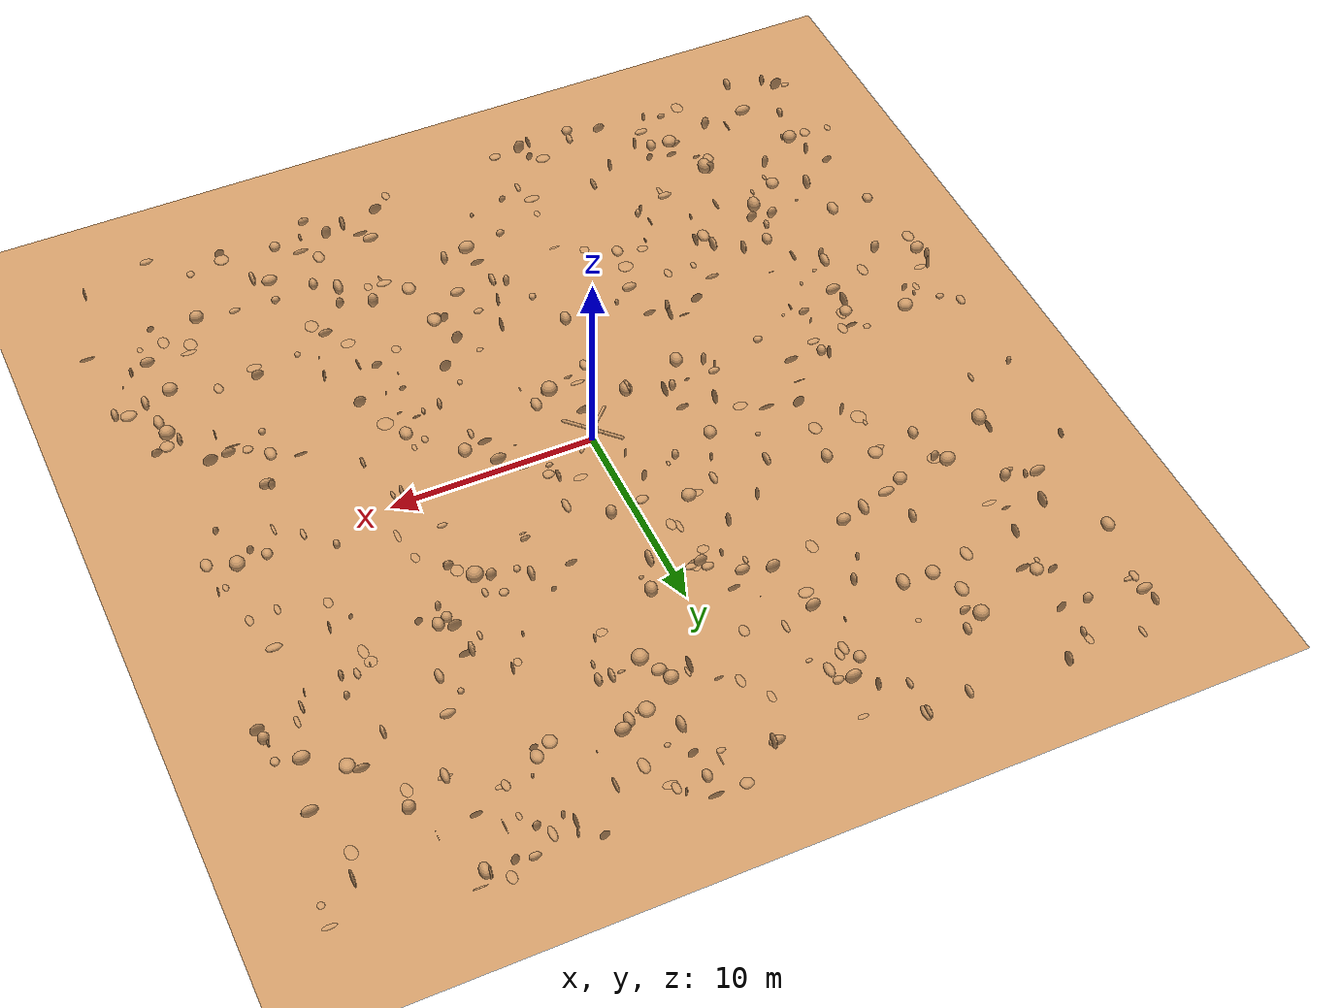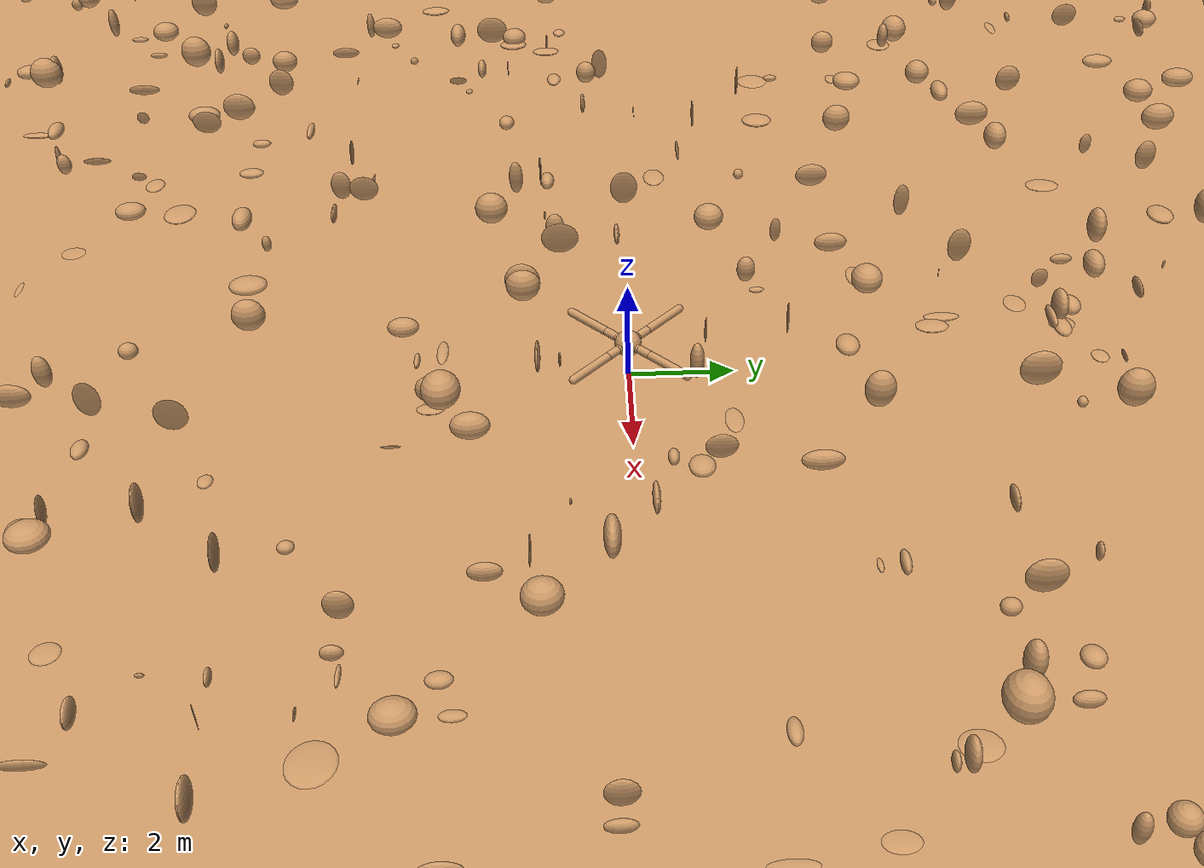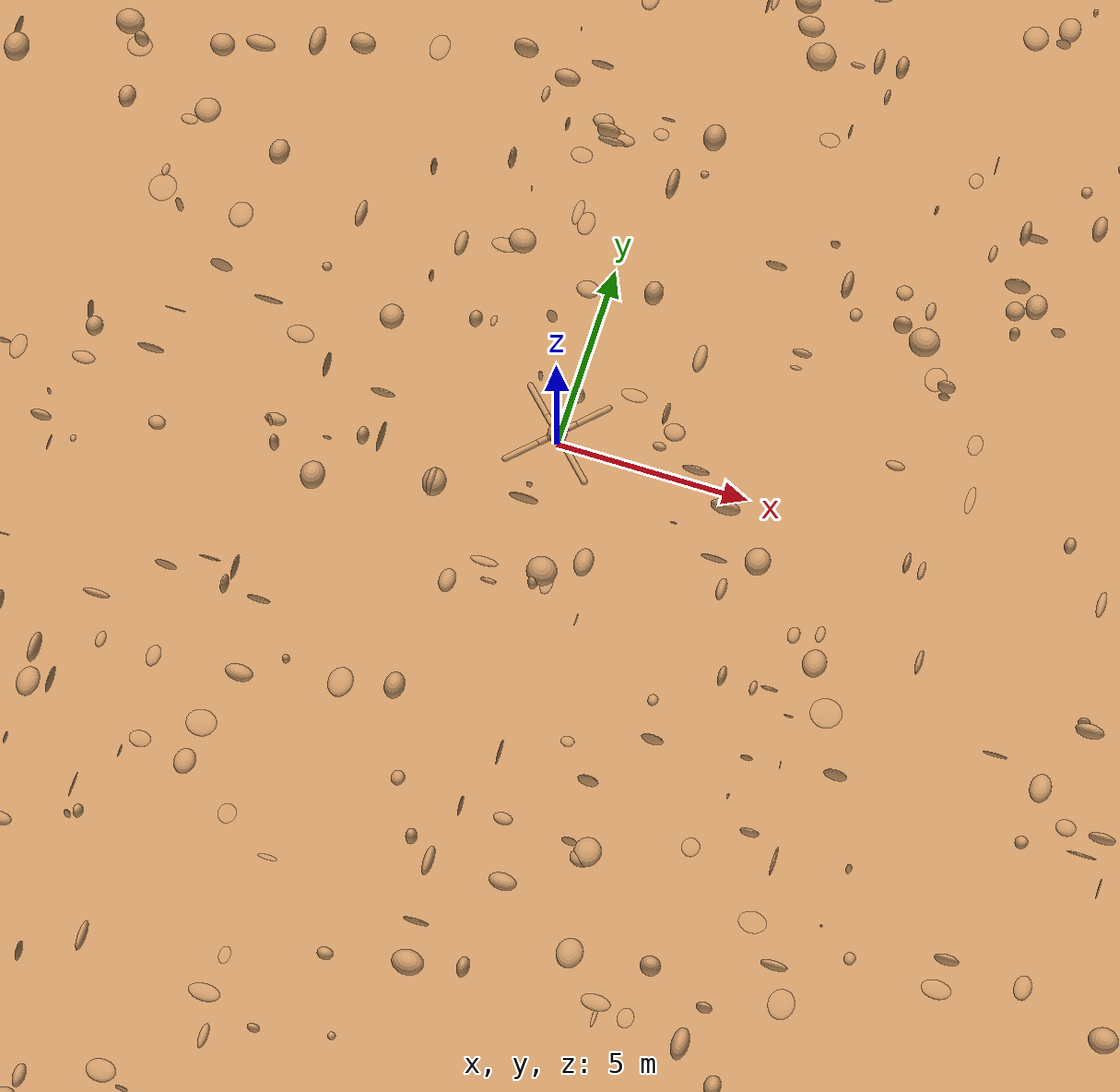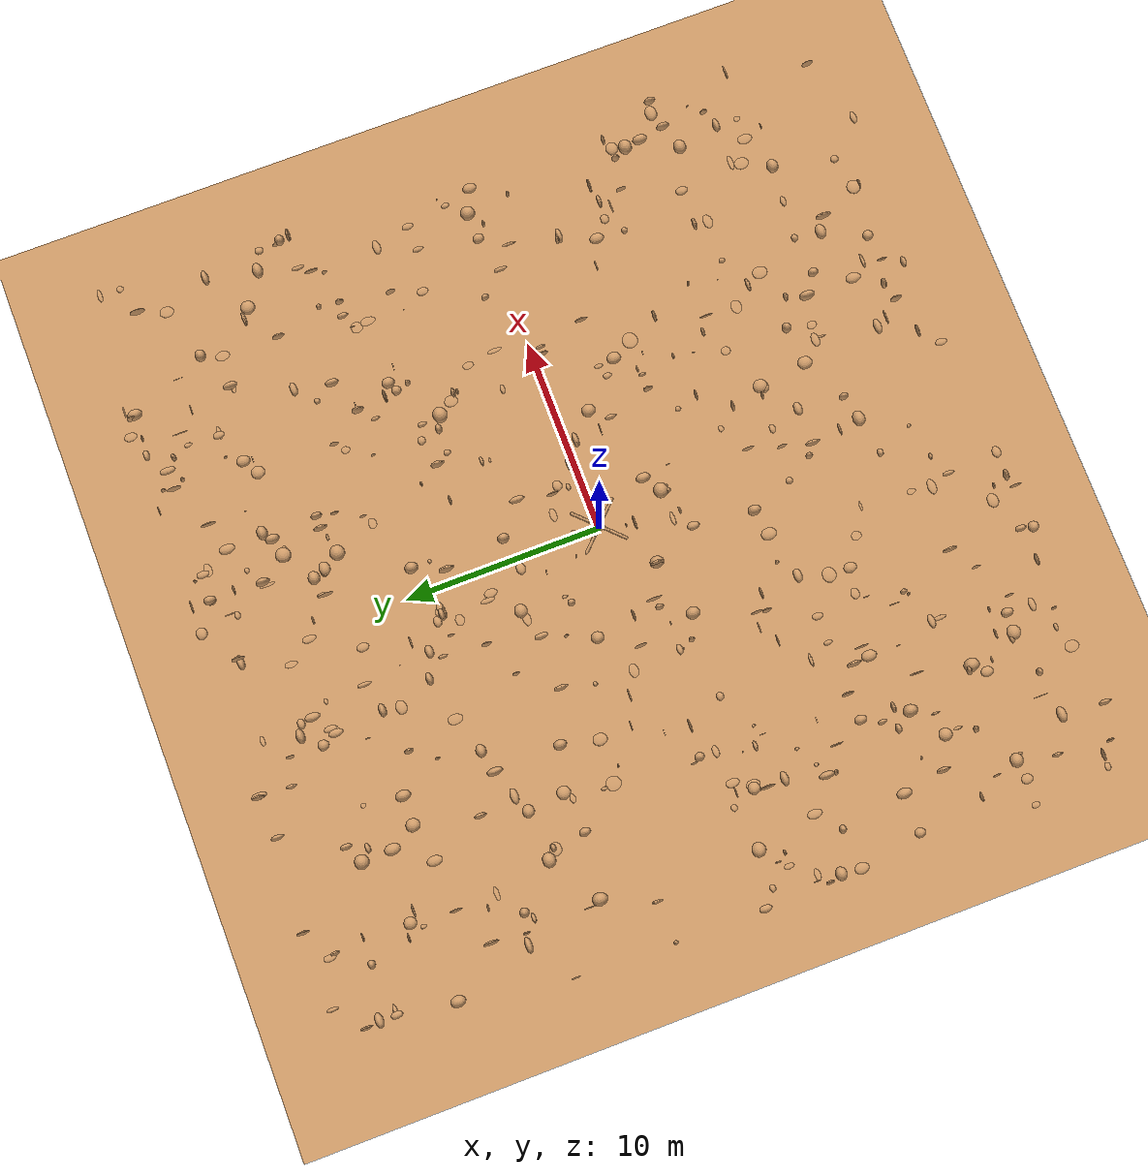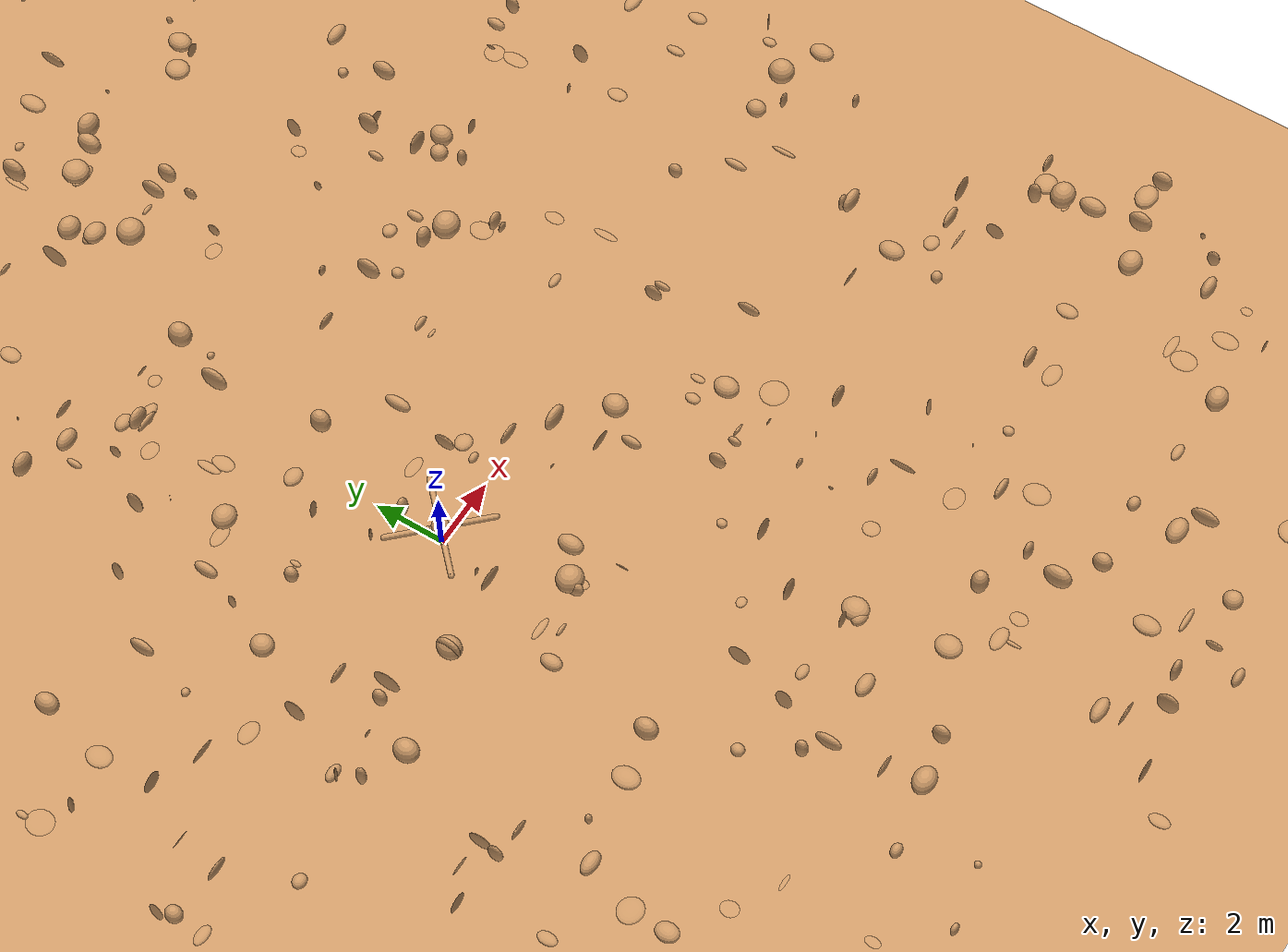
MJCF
<mujoco model="tensegrity default scene">
  <compiler angle="degree" coordinate="local" inertiafromgeom="true" autolimits="true" />
  <option integrator="RK4" timestep="0.01" gravity="0 0 -9.81" />
  <statistic center="0 0 .3" extent="20" />
  <visual>
    <headlight diffuse="0.6 0.6 0.6" ambient="0.3 0.3 0.3" specular="0 0 0" />
    <rgba haze="0.15 0.25 0.35 1" />
    <global azimuth="120" elevation="-20" />
  </visual>
  <asset>
    <texture type="skybox" builtin="gradient" rgb1="0.3 0.5 0.7" rgb2="0 0 0" width="512" height="3072" />
    <texture type="2d" name="groundplane" builtin="checker" mark="edge" rgb1="0.2 0.3 0.4" rgb2="0.1 0.2 0.3" markrgb="0.8 0.8 0.8" width="300" height="300" />
    <material name="groundplane" texture="groundplane" texuniform="true" texrepeat="5 5" reflectance="0.2" />
    <material name="rock" rgba="0.4 0.3 0.2 1" />
  </asset>
  <worldbody>
    <light pos="2.5 0 3" dir="0 0 -1" directional="false" />
    <geom name="floor" size="0 0 0.05" type="plane" material="groundplane" friction="150 150 150" />
    <geom name="rock_0" type="ellipsoid" size="0.11 0.343 0.12" pos="14.14 -0.08 0.12" material="rock" contype="1" conaffinity="1" condim="3" density="500" friction="1 0.5 0.5" />
    <geom name="rock_1" type="ellipsoid" size="0.229 0.036 0.326" pos="-14.54 17.38 0.326" material="rock" contype="1" conaffinity="1" condim="3" density="500" friction="1 0.5 0.5" />
    <geom name="rock_2" type="ellipsoid" size="0.043 0.377 0.111" pos="8.26 -8.81 0.111" material="rock" contype="1" conaffinity="1" condim="3" density="500" friction="1 0.5 0.5" />
    <geom name="rock_3" type="ellipsoid" size="0.209 0.309 0.184" pos="-1.49 -4.34 0.184" material="rock" contype="1" conaffinity="1" condim="3" density="500" friction="1 0.5 0.5" />
    <geom name="rock_4" type="ellipsoid" size="0.143 0.113 0.089" pos="4.1 16.75 0.089" material="rock" contype="1" conaffinity="1" condim="3" density="500" friction="1 0.5 0.5" />
    <geom name="rock_5" type="ellipsoid" size="0.327 0.013 0.218" pos="10.0 9.04 0.218" material="rock" contype="1" conaffinity="1" condim="3" density="500" friction="1 0.5 0.5" />
    <geom name="rock_6" type="ellipsoid" size="0.127 0.145 0.103" pos="4.28 -5.77 0.103" material="rock" contype="1" conaffinity="1" condim="3" density="500" friction="1 0.5 0.5" />
    <geom name="rock_7" type="ellipsoid" size="0.277 0.116 0.398" pos="-4.58 -19.53 0.398" material="rock" contype="1" conaffinity="1" condim="3" density="500" friction="1 0.5 0.5" />
    <geom name="rock_8" type="ellipsoid" size="0.085 0.094 0.281" pos="9.47 18.2 0.281" material="rock" contype="1" conaffinity="1" condim="3" density="500" friction="1 0.5 0.5" />
    <geom name="rock_9" type="ellipsoid" size="0.214 0.174 0.365" pos="-17.79 -5.62 0.365" material="rock" contype="1" conaffinity="1" condim="3" density="500" friction="1 0.5 0.5" />
    <geom name="rock_10" type="ellipsoid" size="0.308 0.146 0.032" pos="-19.35 -3.74 0.032" material="rock" contype="1" conaffinity="1" condim="3" density="500" friction="1 0.5 0.5" />
    <geom name="rock_11" type="ellipsoid" size="0.27 0.262 0.231" pos="-7.4 -19.82 0.231" material="rock" contype="1" conaffinity="1" condim="3" density="500" friction="1 0.5 0.5" />
    <geom name="rock_12" type="ellipsoid" size="0.214 0.311 0.107" pos="14.8 -10.03 0.107" material="rock" contype="1" conaffinity="1" condim="3" density="500" friction="1 0.5 0.5" />
    <geom name="rock_13" type="ellipsoid" size="0.076 0.193 0.344" pos="-18.36 -19.16 0.344" material="rock" contype="1" conaffinity="1" condim="3" density="500" friction="1 0.5 0.5" />
    <geom name="rock_14" type="ellipsoid" size="0.336 0.318 0.137" pos="18.12 -7.53 0.137" material="rock" contype="1" conaffinity="1" condim="3" density="500" friction="1 0.5 0.5" />
    <geom name="rock_15" type="ellipsoid" size="0.294 0.267 0.385" pos="15.09 15.36 0.385" material="rock" contype="1" conaffinity="1" condim="3" density="500" friction="1 0.5 0.5" />
    <geom name="rock_16" type="ellipsoid" size="0.34 0.202 0.264" pos="-2.82 9.82 0.264" material="rock" contype="1" conaffinity="1" condim="3" density="500" friction="1 0.5 0.5" />
    <geom name="rock_17" type="ellipsoid" size="0.383 0.262 0.269" pos="10.29 -15.72 0.269" material="rock" contype="1" conaffinity="1" condim="3" density="500" friction="1 0.5 0.5" />
    <geom name="rock_18" type="ellipsoid" size="0.286 0.029 0.138" pos="-14.34 -1.54 0.138" material="rock" contype="1" conaffinity="1" condim="3" density="500" friction="1 0.5 0.5" />
    <geom name="rock_19" type="ellipsoid" size="0.016 0.163 0.103" pos="-7.74 -10.91 0.103" material="rock" contype="1" conaffinity="1" condim="3" density="500" friction="1 0.5 0.5" />
    <geom name="rock_20" type="ellipsoid" size="0.116 0.363 0.112" pos="-3.19 13.28 0.112" material="rock" contype="1" conaffinity="1" condim="3" density="500" friction="1 0.5 0.5" />
    <geom name="rock_21" type="ellipsoid" size="0.215 0.046 0.098" pos="-15.31 11.4 0.098" material="rock" contype="1" conaffinity="1" condim="3" density="500" friction="1 0.5 0.5" />
    <geom name="rock_22" type="ellipsoid" size="0.081 0.102 0.088" pos="-13.44 -5.04 0.088" material="rock" contype="1" conaffinity="1" condim="3" density="500" friction="1 0.5 0.5" />
    <geom name="rock_23" type="ellipsoid" size="0.054 0.298 0.044" pos="5.26 -13.72 0.044" material="rock" contype="1" conaffinity="1" condim="3" density="500" friction="1 0.5 0.5" />
    <geom name="rock_24" type="ellipsoid" size="0.367 0.342 0.278" pos="-17.28 -1.55 0.278" material="rock" contype="1" conaffinity="1" condim="3" density="500" friction="1 0.5 0.5" />
    <geom name="rock_25" type="ellipsoid" size="0.302 0.308 0.22" pos="-14.48 -2.41 0.22" material="rock" contype="1" conaffinity="1" condim="3" density="500" friction="1 0.5 0.5" />
    <geom name="rock_26" type="ellipsoid" size="0.171 0.187 0.159" pos="-1.05 -9.55 0.159" material="rock" contype="1" conaffinity="1" condim="3" density="500" friction="1 0.5 0.5" />
    <geom name="rock_27" type="ellipsoid" size="0.265 0.207 0.011" pos="4.18 10.26 0.011" material="rock" contype="1" conaffinity="1" condim="3" density="500" friction="1 0.5 0.5" />
    <geom name="rock_28" type="ellipsoid" size="0.012 0.068 0.077" pos="6.92 15.86 0.077" material="rock" contype="1" conaffinity="1" condim="3" density="500" friction="1 0.5 0.5" />
    <geom name="rock_29" type="ellipsoid" size="0.398 0.302 0.176" pos="19.18 -10.04 0.176" material="rock" contype="1" conaffinity="1" condim="3" density="500" friction="1 0.5 0.5" />
    <geom name="rock_30" type="ellipsoid" size="0.388 0.047 0.101" pos="19.9 -14.38 0.101" material="rock" contype="1" conaffinity="1" condim="3" density="500" friction="1 0.5 0.5" />
    <geom name="rock_31" type="ellipsoid" size="0.233 0.235 0.362" pos="-16.13 9.87 0.362" material="rock" contype="1" conaffinity="1" condim="3" density="500" friction="1 0.5 0.5" />
    <geom name="rock_32" type="ellipsoid" size="0.18 0.009 0.072" pos="0.03 9.54 0.072" material="rock" contype="1" conaffinity="1" condim="3" density="500" friction="1 0.5 0.5" />
    <geom name="rock_33" type="ellipsoid" size="0.007 0.006 0.145" pos="-2.76 6.55 0.145" material="rock" contype="1" conaffinity="1" condim="3" density="500" friction="1 0.5 0.5" />
    <geom name="rock_34" type="ellipsoid" size="0.058 0.241 0.153" pos="7.89 -18.07 0.153" material="rock" contype="1" conaffinity="1" condim="3" density="500" friction="1 0.5 0.5" />
    <geom name="rock_35" type="ellipsoid" size="0.251 0.061 0.011" pos="-3.44 -12.36 0.011" material="rock" contype="1" conaffinity="1" condim="3" density="500" friction="1 0.5 0.5" />
    <geom name="rock_36" type="ellipsoid" size="0.348 0.121 0.203" pos="-12.04 -16.7 0.203" material="rock" contype="1" conaffinity="1" condim="3" density="500" friction="1 0.5 0.5" />
    <geom name="rock_37" type="ellipsoid" size="0.091 0.239 0.223" pos="-14.75 18.86 0.223" material="rock" contype="1" conaffinity="1" condim="3" density="500" friction="1 0.5 0.5" />
    <geom name="rock_38" type="ellipsoid" size="0.26 0.351 0.188" pos="18.66 -0.09 0.188" material="rock" contype="1" conaffinity="1" condim="3" density="500" friction="1 0.5 0.5" />
    <geom name="rock_39" type="ellipsoid" size="0.099 0.26 0.256" pos="-18.11 -16.56 0.256" material="rock" contype="1" conaffinity="1" condim="3" density="500" friction="1 0.5 0.5" />
    <geom name="rock_40" type="ellipsoid" size="0.035 0.238 0.352" pos="14.9 5.47 0.352" material="rock" contype="1" conaffinity="1" condim="3" density="500" friction="1 0.5 0.5" />
    <geom name="rock_41" type="ellipsoid" size="0.113 0.368 0.021" pos="10.31 1.66 0.021" material="rock" contype="1" conaffinity="1" condim="3" density="500" friction="1 0.5 0.5" />
    <geom name="rock_42" type="ellipsoid" size="0.302 0.052 0.165" pos="-5.79 -6.21 0.165" material="rock" contype="1" conaffinity="1" condim="3" density="500" friction="1 0.5 0.5" />
    <geom name="rock_43" type="ellipsoid" size="0.178 0.109 0.318" pos="10.67 18.25 0.318" material="rock" contype="1" conaffinity="1" condim="3" density="500" friction="1 0.5 0.5" />
    <geom name="rock_44" type="ellipsoid" size="0.101 0.274 0.187" pos="-6.6 18.17 0.187" material="rock" contype="1" conaffinity="1" condim="3" density="500" friction="1 0.5 0.5" />
    <geom name="rock_45" type="ellipsoid" size="0.131 0.1 0.341" pos="-15.17 -6.33 0.341" material="rock" contype="1" conaffinity="1" condim="3" density="500" friction="1 0.5 0.5" />
    <geom name="rock_46" type="ellipsoid" size="0.353 0.118 0.014" pos="-14.8 10.79 0.014" material="rock" contype="1" conaffinity="1" condim="3" density="500" friction="1 0.5 0.5" />
    <geom name="rock_47" type="ellipsoid" size="0.254 0.319 0.154" pos="-13.2 -14.98 0.154" material="rock" contype="1" conaffinity="1" condim="3" density="500" friction="1 0.5 0.5" />
    <geom name="rock_48" type="ellipsoid" size="0.152 0.051 0.139" pos="6.89 -6.51 0.139" material="rock" contype="1" conaffinity="1" condim="3" density="500" friction="1 0.5 0.5" />
    <geom name="rock_49" type="ellipsoid" size="0.351 0.055 0.193" pos="-10.61 -0.64 0.193" material="rock" contype="1" conaffinity="1" condim="3" density="500" friction="1 0.5 0.5" />
    <geom name="rock_50" type="ellipsoid" size="0.365 0.277 0.1" pos="-5.48 -18.5 0.1" material="rock" contype="1" conaffinity="1" condim="3" density="500" friction="1 0.5 0.5" />
    <geom name="rock_51" type="ellipsoid" size="0.213 0.388 0.019" pos="13.96 7.02 0.019" material="rock" contype="1" conaffinity="1" condim="3" density="500" friction="1 0.5 0.5" />
    <geom name="rock_52" type="ellipsoid" size="0.343 0.166 0.116" pos="-10.93 -18.29 0.116" material="rock" contype="1" conaffinity="1" condim="3" density="500" friction="1 0.5 0.5" />
    <geom name="rock_53" type="ellipsoid" size="0.099 0.048 0.065" pos="-15.96 -10.44 0.065" material="rock" contype="1" conaffinity="1" condim="3" density="500" friction="1 0.5 0.5" />
    <geom name="rock_54" type="ellipsoid" size="0.124 0.122 0.017" pos="-8.65 15.29 0.017" material="rock" contype="1" conaffinity="1" condim="3" density="500" friction="1 0.5 0.5" />
    <geom name="rock_55" type="ellipsoid" size="0.16 0.092 0.199" pos="-2.36 -16.47 0.199" material="rock" contype="1" conaffinity="1" condim="3" density="500" friction="1 0.5 0.5" />
    <geom name="rock_56" type="ellipsoid" size="0.127 0.306 0.381" pos="9.74 9.03 0.381" material="rock" contype="1" conaffinity="1" condim="3" density="500" friction="1 0.5 0.5" />
    <geom name="rock_57" type="ellipsoid" size="0.385 0.344 0.073" pos="-6.09 -9.64 0.073" material="rock" contype="1" conaffinity="1" condim="3" density="500" friction="1 0.5 0.5" />
    <geom name="rock_58" type="ellipsoid" size="0.191 0.007 0.231" pos="9.26 14.67 0.231" material="rock" contype="1" conaffinity="1" condim="3" density="500" friction="1 0.5 0.5" />
    <geom name="rock_59" type="ellipsoid" size="0.078 0.22 0.06" pos="-15.23 -12.63 0.06" material="rock" contype="1" conaffinity="1" condim="3" density="500" friction="1 0.5 0.5" />
    <geom name="rock_60" type="ellipsoid" size="0.355 0.275 0.1" pos="-4.86 12.0 0.1" material="rock" contype="1" conaffinity="1" condim="3" density="500" friction="1 0.5 0.5" />
    <geom name="rock_61" type="ellipsoid" size="0.24 0.151 0.106" pos="1.7 -9.75 0.106" material="rock" contype="1" conaffinity="1" condim="3" density="500" friction="1 0.5 0.5" />
    <geom name="rock_62" type="ellipsoid" size="0.34 0.171 0.025" pos="1.45 1.86 0.025" material="rock" contype="1" conaffinity="1" condim="3" density="500" friction="1 0.5 0.5" />
    <geom name="rock_63" type="ellipsoid" size="0.26 0.375 0.045" pos="-6.31 9.77 0.045" material="rock" contype="1" conaffinity="1" condim="3" density="500" friction="1 0.5 0.5" />
    <geom name="rock_64" type="ellipsoid" size="0.157 0.093 0.061" pos="-3.3 15.29 0.061" material="rock" contype="1" conaffinity="1" condim="3" density="500" friction="1 0.5 0.5" />
    <geom name="rock_65" type="ellipsoid" size="0.211 0.39 0.188" pos="-3.81 16.15 0.188" material="rock" contype="1" conaffinity="1" condim="3" density="500" friction="1 0.5 0.5" />
    <geom name="rock_66" type="ellipsoid" size="0.155 0.284 0.327" pos="5.43 12.69 0.327" material="rock" contype="1" conaffinity="1" condim="3" density="500" friction="1 0.5 0.5" />
    <geom name="rock_67" type="ellipsoid" size="0.154 0.218 0.103" pos="7.1 -3.12 0.103" material="rock" contype="1" conaffinity="1" condim="3" density="500" friction="1 0.5 0.5" />
    <geom name="rock_68" type="ellipsoid" size="0.192 0.13 0.333" pos="-13.77 7.53 0.333" material="rock" contype="1" conaffinity="1" condim="3" density="500" friction="1 0.5 0.5" />
    <geom name="rock_69" type="ellipsoid" size="0.378 0.323 0.333" pos="-14.23 7.92 0.333" material="rock" contype="1" conaffinity="1" condim="3" density="500" friction="1 0.5 0.5" />
    <geom name="rock_70" type="ellipsoid" size="0.092 0.388 0.382" pos="-16.9 11.82 0.382" material="rock" contype="1" conaffinity="1" condim="3" density="500" friction="1 0.5 0.5" />
    <geom name="rock_71" type="ellipsoid" size="0.198 0.096 0.149" pos="-12.38 -18.93 0.149" material="rock" contype="1" conaffinity="1" condim="3" density="500" friction="1 0.5 0.5" />
    <geom name="rock_72" type="ellipsoid" size="0.009 0.007 0.312" pos="7.73 -6.49 0.312" material="rock" contype="1" conaffinity="1" condim="3" density="500" friction="1 0.5 0.5" />
    <geom name="rock_73" type="ellipsoid" size="0.081 0.259 0.28" pos="9.26 -0.52 0.28" material="rock" contype="1" conaffinity="1" condim="3" density="500" friction="1 0.5 0.5" />
    <geom name="rock_74" type="ellipsoid" size="0.271 0.105 0.216" pos="-12.62 -3.21 0.216" material="rock" contype="1" conaffinity="1" condim="3" density="500" friction="1 0.5 0.5" />
    <geom name="rock_75" type="ellipsoid" size="0.179 0.295 0.065" pos="2.89 -19.22 0.065" material="rock" contype="1" conaffinity="1" condim="3" density="500" friction="1 0.5 0.5" />
    <geom name="rock_76" type="ellipsoid" size="0.275 0.209 0.055" pos="-7.39 -10.47 0.055" material="rock" contype="1" conaffinity="1" condim="3" density="500" friction="1 0.5 0.5" />
    <geom name="rock_77" type="ellipsoid" size="0.303 0.101 0.302" pos="12.88 -9.96 0.302" material="rock" contype="1" conaffinity="1" condim="3" density="500" friction="1 0.5 0.5" />
    <geom name="rock_78" type="ellipsoid" size="0.121 0.374 0.249" pos="0.32 -11.33 0.249" material="rock" contype="1" conaffinity="1" condim="3" density="500" friction="1 0.5 0.5" />
    <geom name="rock_79" type="ellipsoid" size="0.329 0.154 0.118" pos="15.38 -19.55 0.118" material="rock" contype="1" conaffinity="1" condim="3" density="500" friction="1 0.5 0.5" />
    <geom name="rock_80" type="ellipsoid" size="0.165 0.173 0.049" pos="19.87 18.01 0.049" material="rock" contype="1" conaffinity="1" condim="3" density="500" friction="1 0.5 0.5" />
    <geom name="rock_81" type="ellipsoid" size="0.339 0.293 0.322" pos="2.55 13.82 0.322" material="rock" contype="1" conaffinity="1" condim="3" density="500" friction="1 0.5 0.5" />
    <geom name="rock_82" type="ellipsoid" size="0.131 0.076 0.253" pos="17.67 -1.77 0.253" material="rock" contype="1" conaffinity="1" condim="3" density="500" friction="1 0.5 0.5" />
    <geom name="rock_83" type="ellipsoid" size="0.227 0.261 0.028" pos="-1.11 8.66 0.028" material="rock" contype="1" conaffinity="1" condim="3" density="500" friction="1 0.5 0.5" />
    <geom name="rock_84" type="ellipsoid" size="0.138 0.007 0.36" pos="-1.14 3.18 0.36" material="rock" contype="1" conaffinity="1" condim="3" density="500" friction="1 0.5 0.5" />
    <geom name="rock_85" type="ellipsoid" size="0.208 0.149 0.071" pos="-19.47 -18.62 0.071" material="rock" contype="1" conaffinity="1" condim="3" density="500" friction="1 0.5 0.5" />
    <geom name="rock_86" type="ellipsoid" size="0.152 0.27 0.276" pos="0.57 -3.68 0.276" material="rock" contype="1" conaffinity="1" condim="3" density="500" friction="1 0.5 0.5" />
    <geom name="rock_87" type="ellipsoid" size="0.163 0.066 0.27" pos="16.62 -0.09 0.27" material="rock" contype="1" conaffinity="1" condim="3" density="500" friction="1 0.5 0.5" />
    <geom name="rock_88" type="ellipsoid" size="0.37 0.193 0.276" pos="-14.57 -3.93 0.276" material="rock" contype="1" conaffinity="1" condim="3" density="500" friction="1 0.5 0.5" />
    <geom name="rock_89" type="ellipsoid" size="0.177 0.28 0.083" pos="-7.79 -8.36 0.083" material="rock" contype="1" conaffinity="1" condim="3" density="500" friction="1 0.5 0.5" />
    <geom name="rock_90" type="ellipsoid" size="0.324 0.177 0.382" pos="-4.09 10.27 0.382" material="rock" contype="1" conaffinity="1" condim="3" density="500" friction="1 0.5 0.5" />
    <geom name="rock_91" type="ellipsoid" size="0.067 0.293 0.262" pos="2.4 1.53 0.262" material="rock" contype="1" conaffinity="1" condim="3" density="500" friction="1 0.5 0.5" />
    <geom name="rock_92" type="ellipsoid" size="0.304 0.361 0.088" pos="-9.68 3.62 0.088" material="rock" contype="1" conaffinity="1" condim="3" density="500" friction="1 0.5 0.5" />
    <geom name="rock_93" type="ellipsoid" size="0.368 0.034 0.048" pos="15.3 -6.41 0.048" material="rock" contype="1" conaffinity="1" condim="3" density="500" friction="1 0.5 0.5" />
    <geom name="rock_94" type="ellipsoid" size="0.164 0.187 0.283" pos="-2.98 2.57 0.283" material="rock" contype="1" conaffinity="1" condim="3" density="500" friction="1 0.5 0.5" />
    <geom name="rock_95" type="ellipsoid" size="0.049 0.074 0.3" pos="4.43 19.27 0.3" material="rock" contype="1" conaffinity="1" condim="3" density="500" friction="1 0.5 0.5" />
    <geom name="rock_96" type="ellipsoid" size="0.148 0.06 0.164" pos="8.94 4.11 0.164" material="rock" contype="1" conaffinity="1" condim="3" density="500" friction="1 0.5 0.5" />
    <geom name="rock_97" type="ellipsoid" size="0.225 0.142 0.045" pos="-11.87 5.83 0.045" material="rock" contype="1" conaffinity="1" condim="3" density="500" friction="1 0.5 0.5" />
    <geom name="rock_98" type="ellipsoid" size="0.19 0.147 0.116" pos="-19.19 -1.51 0.116" material="rock" contype="1" conaffinity="1" condim="3" density="500" friction="1 0.5 0.5" />
    <geom name="rock_99" type="ellipsoid" size="0.366 0.361 0.355" pos="-11.18 16.24 0.355" material="rock" contype="1" conaffinity="1" condim="3" density="500" friction="1 0.5 0.5" />
    <geom name="rock_100" type="ellipsoid" size="0.159 0.387 0.191" pos="2.77 3.26 0.191" material="rock" contype="1" conaffinity="1" condim="3" density="500" friction="1 0.5 0.5" />
    <geom name="rock_101" type="ellipsoid" size="0.375 0.205 0.279" pos="-18.41 17.95 0.279" material="rock" contype="1" conaffinity="1" condim="3" density="500" friction="1 0.5 0.5" />
    <geom name="rock_102" type="ellipsoid" size="0.176 0.014 0.267" pos="11.24 6.64 0.267" material="rock" contype="1" conaffinity="1" condim="3" density="500" friction="1 0.5 0.5" />
    <geom name="rock_103" type="ellipsoid" size="0.163 0.337 0.345" pos="18.26 -10.33 0.345" material="rock" contype="1" conaffinity="1" condim="3" density="500" friction="1 0.5 0.5" />
    <geom name="rock_104" type="ellipsoid" size="0.128 0.356 0.399" pos="-2.64 -2.02 0.399" material="rock" contype="1" conaffinity="1" condim="3" density="500" friction="1 0.5 0.5" />
    <geom name="rock_105" type="ellipsoid" size="0.318 0.381 0.372" pos="-16.8 6.32 0.372" material="rock" contype="1" conaffinity="1" condim="3" density="500" friction="1 0.5 0.5" />
    <geom name="rock_106" type="ellipsoid" size="0.385 0.148 0.337" pos="4.54 -0.47 0.337" material="rock" contype="1" conaffinity="1" condim="3" density="500" friction="1 0.5 0.5" />
    <geom name="rock_107" type="ellipsoid" size="0.351 0.069 0.199" pos="3.55 0.31 0.199" material="rock" contype="1" conaffinity="1" condim="3" density="500" friction="1 0.5 0.5" />
    <geom name="rock_108" type="ellipsoid" size="0.363 0.155 0.306" pos="14.69 -3.4 0.306" material="rock" contype="1" conaffinity="1" condim="3" density="500" friction="1 0.5 0.5" />
    <geom name="rock_109" type="ellipsoid" size="0.287 0.345 0.21" pos="9.32 15.13 0.21" material="rock" contype="1" conaffinity="1" condim="3" density="500" friction="1 0.5 0.5" />
    <geom name="rock_110" type="ellipsoid" size="0.325 0.046 0.306" pos="3.79 -18.3 0.306" material="rock" contype="1" conaffinity="1" condim="3" density="500" friction="1 0.5 0.5" />
    <geom name="rock_111" type="ellipsoid" size="0.253 0.129 0.254" pos="-10.66 15.76 0.254" material="rock" contype="1" conaffinity="1" condim="3" density="500" friction="1 0.5 0.5" />
    <geom name="rock_112" type="ellipsoid" size="0.213 0.298 0.28" pos="3.31 18.9 0.28" material="rock" contype="1" conaffinity="1" condim="3" density="500" friction="1 0.5 0.5" />
    <geom name="rock_113" type="ellipsoid" size="0.387 0.033 0.135" pos="-8.21 1.55 0.135" material="rock" contype="1" conaffinity="1" condim="3" density="500" friction="1 0.5 0.5" />
    <geom name="rock_114" type="ellipsoid" size="0.094 0.324 0.391" pos="0.08 18.55 0.391" material="rock" contype="1" conaffinity="1" condim="3" density="500" friction="1 0.5 0.5" />
    <geom name="rock_115" type="ellipsoid" size="0.276 0.13 0.223" pos="7.37 -19.01 0.223" material="rock" contype="1" conaffinity="1" condim="3" density="500" friction="1 0.5 0.5" />
    <geom name="rock_116" type="ellipsoid" size="0.25 0.066 0.205" pos="-18.7 -12.4 0.205" material="rock" contype="1" conaffinity="1" condim="3" density="500" friction="1 0.5 0.5" />
    <geom name="rock_117" type="ellipsoid" size="0.26 0.118 0.373" pos="-12.83 -14.14 0.373" material="rock" contype="1" conaffinity="1" condim="3" density="500" friction="1 0.5 0.5" />
    <geom name="rock_118" type="ellipsoid" size="0.39 0.134 0.039" pos="15.34 -12.88 0.039" material="rock" contype="1" conaffinity="1" condim="3" density="500" friction="1 0.5 0.5" />
    <geom name="rock_119" type="ellipsoid" size="0.021 0.397 0.042" pos="11.8 17.59 0.042" material="rock" contype="1" conaffinity="1" condim="3" density="500" friction="1 0.5 0.5" />
    <geom name="rock_120" type="ellipsoid" size="0.334 0.341 0.195" pos="-11.47 6.15 0.195" material="rock" contype="1" conaffinity="1" condim="3" density="500" friction="1 0.5 0.5" />
    <geom name="rock_121" type="ellipsoid" size="0.157 0.092 0.312" pos="14.5 -3.25 0.312" material="rock" contype="1" conaffinity="1" condim="3" density="500" friction="1 0.5 0.5" />
    <geom name="rock_122" type="ellipsoid" size="0.356 0.364 0.333" pos="17.4 0.46 0.333" material="rock" contype="1" conaffinity="1" condim="3" density="500" friction="1 0.5 0.5" />
    <geom name="rock_123" type="ellipsoid" size="0.249 0.212 0.097" pos="14.77 -5.88 0.097" material="rock" contype="1" conaffinity="1" condim="3" density="500" friction="1 0.5 0.5" />
    <geom name="rock_124" type="ellipsoid" size="0.261 0.186 0.166" pos="-3.93 16.76 0.166" material="rock" contype="1" conaffinity="1" condim="3" density="500" friction="1 0.5 0.5" />
    <geom name="rock_125" type="ellipsoid" size="0.07 0.397 0.358" pos="-14.66 -3.01 0.358" material="rock" contype="1" conaffinity="1" condim="3" density="500" friction="1 0.5 0.5" />
    <geom name="rock_126" type="ellipsoid" size="0.293 0.077 0.345" pos="9.08 -6.35 0.345" material="rock" contype="1" conaffinity="1" condim="3" density="500" friction="1 0.5 0.5" />
    <geom name="rock_127" type="ellipsoid" size="0.086 0.277 0.075" pos="1.7 13.71 0.075" material="rock" contype="1" conaffinity="1" condim="3" density="500" friction="1 0.5 0.5" />
    <geom name="rock_128" type="ellipsoid" size="0.268 0.238 0.117" pos="2.73 1.16 0.117" material="rock" contype="1" conaffinity="1" condim="3" density="500" friction="1 0.5 0.5" />
    <geom name="rock_129" type="ellipsoid" size="0.105 0.093 0.103" pos="1.38 8.29 0.103" material="rock" contype="1" conaffinity="1" condim="3" density="500" friction="1 0.5 0.5" />
    <geom name="rock_130" type="ellipsoid" size="0.038 0.011 0.358" pos="18.67 1.66 0.358" material="rock" contype="1" conaffinity="1" condim="3" density="500" friction="1 0.5 0.5" />
    <geom name="rock_131" type="ellipsoid" size="0.099 0.245 0.291" pos="5.73 -4.73 0.291" material="rock" contype="1" conaffinity="1" condim="3" density="500" friction="1 0.5 0.5" />
    <geom name="rock_132" type="ellipsoid" size="0.006 0.212 0.098" pos="-12.2 -3.82 0.098" material="rock" contype="1" conaffinity="1" condim="3" density="500" friction="1 0.5 0.5" />
    <geom name="rock_133" type="ellipsoid" size="0.052 0.022 0.374" pos="-7.04 -1.67 0.374" material="rock" contype="1" conaffinity="1" condim="3" density="500" friction="1 0.5 0.5" />
    <geom name="rock_134" type="ellipsoid" size="0.3 0.318 0.281" pos="-5.04 1.99 0.281" material="rock" contype="1" conaffinity="1" condim="3" density="500" friction="1 0.5 0.5" />
    <geom name="rock_135" type="ellipsoid" size="0.048 0.17 0.223" pos="-2.42 8.56 0.223" material="rock" contype="1" conaffinity="1" condim="3" density="500" friction="1 0.5 0.5" />
    <geom name="rock_136" type="ellipsoid" size="0.366 0.049 0.206" pos="-14.19 14.74 0.206" material="rock" contype="1" conaffinity="1" condim="3" density="500" friction="1 0.5 0.5" />
    <geom name="rock_137" type="ellipsoid" size="0.264 0.381 0.146" pos="7.5 -16.37 0.146" material="rock" contype="1" conaffinity="1" condim="3" density="500" friction="1 0.5 0.5" />
    <geom name="rock_138" type="ellipsoid" size="0.286 0.366 0.024" pos="-13.48 -19.31 0.024" material="rock" contype="1" conaffinity="1" condim="3" density="500" friction="1 0.5 0.5" />
    <geom name="rock_139" type="ellipsoid" size="0.076 0.022 0.037" pos="3.41 -1.14 0.037" material="rock" contype="1" conaffinity="1" condim="3" density="500" friction="1 0.5 0.5" />
    <geom name="rock_140" type="ellipsoid" size="0.178 0.292 0.099" pos="11.02 15.84 0.099" material="rock" contype="1" conaffinity="1" condim="3" density="500" friction="1 0.5 0.5" />
    <geom name="rock_141" type="ellipsoid" size="0.181 0.39 0.28" pos="-15.13 -5.88 0.28" material="rock" contype="1" conaffinity="1" condim="3" density="500" friction="1 0.5 0.5" />
    <geom name="rock_142" type="ellipsoid" size="0.213 0.242 0.275" pos="-12.16 -0.52 0.275" material="rock" contype="1" conaffinity="1" condim="3" density="500" friction="1 0.5 0.5" />
    <geom name="rock_143" type="ellipsoid" size="0.181 0.217 0.035" pos="8.12 10.25 0.035" material="rock" contype="1" conaffinity="1" condim="3" density="500" friction="1 0.5 0.5" />
    <geom name="rock_144" type="ellipsoid" size="0.282 0.357 0.033" pos="17.93 16.21 0.033" material="rock" contype="1" conaffinity="1" condim="3" density="500" friction="1 0.5 0.5" />
    <geom name="rock_145" type="ellipsoid" size="0.168 0.334 0.087" pos="-4.64 15.53 0.087" material="rock" contype="1" conaffinity="1" condim="3" density="500" friction="1 0.5 0.5" />
    <geom name="rock_146" type="ellipsoid" size="0.348 0.321 0.319" pos="-17.67 -14.61 0.319" material="rock" contype="1" conaffinity="1" condim="3" density="500" friction="1 0.5 0.5" />
    <geom name="rock_147" type="ellipsoid" size="0.124 0.157 0.242" pos="-8.16 -12.69 0.242" material="rock" contype="1" conaffinity="1" condim="3" density="500" friction="1 0.5 0.5" />
    <geom name="rock_148" type="ellipsoid" size="0.135 0.203 0.083" pos="18.26 1.36 0.083" material="rock" contype="1" conaffinity="1" condim="3" density="500" friction="1 0.5 0.5" />
    <geom name="rock_149" type="ellipsoid" size="0.18 0.338 0.296" pos="11.52 9.75 0.296" material="rock" contype="1" conaffinity="1" condim="3" density="500" friction="1 0.5 0.5" />
    <geom name="rock_150" type="ellipsoid" size="0.021 0.069 0.123" pos="18.89 -11.92 0.123" material="rock" contype="1" conaffinity="1" condim="3" density="500" friction="1 0.5 0.5" />
    <geom name="rock_151" type="ellipsoid" size="0.011 0.31 0.35" pos="1.13 -8.24 0.35" material="rock" contype="1" conaffinity="1" condim="3" density="500" friction="1 0.5 0.5" />
    <geom name="rock_152" type="ellipsoid" size="0.042 0.155 0.118" pos="-18.14 -2.22 0.118" material="rock" contype="1" conaffinity="1" condim="3" density="500" friction="1 0.5 0.5" />
    <geom name="rock_153" type="ellipsoid" size="0.043 0.206 0.338" pos="-10.14 -17.38 0.338" material="rock" contype="1" conaffinity="1" condim="3" density="500" friction="1 0.5 0.5" />
    <geom name="rock_154" type="ellipsoid" size="0.321 0.026 0.101" pos="12.65 -4.61 0.101" material="rock" contype="1" conaffinity="1" condim="3" density="500" friction="1 0.5 0.5" />
    <geom name="rock_155" type="ellipsoid" size="0.213 0.047 0.099" pos="0.65 14.56 0.099" material="rock" contype="1" conaffinity="1" condim="3" density="500" friction="1 0.5 0.5" />
    <geom name="rock_156" type="ellipsoid" size="0.155 0.119 0.395" pos="-15.61 -13.36 0.395" material="rock" contype="1" conaffinity="1" condim="3" density="500" friction="1 0.5 0.5" />
    <geom name="rock_157" type="ellipsoid" size="0.076 0.154 0.048" pos="-2.56 2.75 0.048" material="rock" contype="1" conaffinity="1" condim="3" density="500" friction="1 0.5 0.5" />
    <geom name="rock_158" type="ellipsoid" size="0.281 0.043 0.358" pos="4.58 -6.82 0.358" material="rock" contype="1" conaffinity="1" condim="3" density="500" friction="1 0.5 0.5" />
    <geom name="rock_159" type="ellipsoid" size="0.231 0.016 0.017" pos="-12.49 -6.43 0.017" material="rock" contype="1" conaffinity="1" condim="3" density="500" friction="1 0.5 0.5" />
    <geom name="rock_160" type="ellipsoid" size="0.199 0.361 0.141" pos="-4.92 15.35 0.141" material="rock" contype="1" conaffinity="1" condim="3" density="500" friction="1 0.5 0.5" />
    <geom name="rock_161" type="ellipsoid" size="0.14 0.158 0.113" pos="10.67 -10.58 0.113" material="rock" contype="1" conaffinity="1" condim="3" density="500" friction="1 0.5 0.5" />
    <geom name="rock_162" type="ellipsoid" size="0.334 0.387 0.383" pos="-12.66 -14.35 0.383" material="rock" contype="1" conaffinity="1" condim="3" density="500" friction="1 0.5 0.5" />
    <geom name="rock_163" type="ellipsoid" size="0.35 0.083 0.116" pos="-9.68 -7.25 0.116" material="rock" contype="1" conaffinity="1" condim="3" density="500" friction="1 0.5 0.5" />
    <geom name="rock_164" type="ellipsoid" size="0.26 0.074 0.246" pos="18.68 -7.26 0.246" material="rock" contype="1" conaffinity="1" condim="3" density="500" friction="1 0.5 0.5" />
    <geom name="rock_165" type="ellipsoid" size="0.252 0.329 0.337" pos="-1.85 -7.38 0.337" material="rock" contype="1" conaffinity="1" condim="3" density="500" friction="1 0.5 0.5" />
    <geom name="rock_166" type="ellipsoid" size="0.167 0.01 0.183" pos="16.58 -14.98 0.183" material="rock" contype="1" conaffinity="1" condim="3" density="500" friction="1 0.5 0.5" />
    <geom name="rock_167" type="ellipsoid" size="0.137 0.277 0.166" pos="14.63 8.1 0.166" material="rock" contype="1" conaffinity="1" condim="3" density="500" friction="1 0.5 0.5" />
    <geom name="rock_168" type="ellipsoid" size="0.005 0.289 0.033" pos="14.46 16.86 0.033" material="rock" contype="1" conaffinity="1" condim="3" density="500" friction="1 0.5 0.5" />
    <geom name="rock_169" type="ellipsoid" size="0.146 0.29 0.212" pos="-7.26 -19.21 0.212" material="rock" contype="1" conaffinity="1" condim="3" density="500" friction="1 0.5 0.5" />
    <geom name="rock_170" type="ellipsoid" size="0.033 0.233 0.348" pos="-8.29 -16.41 0.348" material="rock" contype="1" conaffinity="1" condim="3" density="500" friction="1 0.5 0.5" />
    <geom name="rock_171" type="ellipsoid" size="0.034 0.338 0.284" pos="-9.95 -9.76 0.284" material="rock" contype="1" conaffinity="1" condim="3" density="500" friction="1 0.5 0.5" />
    <geom name="rock_172" type="ellipsoid" size="0.121 0.11 0.114" pos="-7.09 2.88 0.114" material="rock" contype="1" conaffinity="1" condim="3" density="500" friction="1 0.5 0.5" />
    <geom name="rock_173" type="ellipsoid" size="0.337 0.1 0.22" pos="8.99 -11.31 0.22" material="rock" contype="1" conaffinity="1" condim="3" density="500" friction="1 0.5 0.5" />
    <geom name="rock_174" type="ellipsoid" size="0.244 0.398 0.14" pos="5.44 17.31 0.14" material="rock" contype="1" conaffinity="1" condim="3" density="500" friction="1 0.5 0.5" />
    <geom name="rock_175" type="ellipsoid" size="0.324 0.377 0.059" pos="9.42 -12.13 0.059" material="rock" contype="1" conaffinity="1" condim="3" density="500" friction="1 0.5 0.5" />
    <geom name="rock_176" type="ellipsoid" size="0.065 0.328 0.314" pos="-14.89 12.86 0.314" material="rock" contype="1" conaffinity="1" condim="3" density="500" friction="1 0.5 0.5" />
    <geom name="rock_177" type="ellipsoid" size="0.28 0.218 0.182" pos="3.8 -10.15 0.182" material="rock" contype="1" conaffinity="1" condim="3" density="500" friction="1 0.5 0.5" />
    <geom name="rock_178" type="ellipsoid" size="0.042 0.116 0.174" pos="7.37 9.07 0.174" material="rock" contype="1" conaffinity="1" condim="3" density="500" friction="1 0.5 0.5" />
    <geom name="rock_179" type="ellipsoid" size="0.225 0.239 0.043" pos="6.24 -9.06 0.043" material="rock" contype="1" conaffinity="1" condim="3" density="500" friction="1 0.5 0.5" />
    <geom name="rock_180" type="ellipsoid" size="0.059 0.219 0.071" pos="-14.19 -11.89 0.071" material="rock" contype="1" conaffinity="1" condim="3" density="500" friction="1 0.5 0.5" />
    <geom name="rock_181" type="ellipsoid" size="0.39 0.192 0.22" pos="4.71 -16.54 0.22" material="rock" contype="1" conaffinity="1" condim="3" density="500" friction="1 0.5 0.5" />
    <geom name="rock_182" type="ellipsoid" size="0.357 0.207 0.21" pos="-5.61 -8.18 0.21" material="rock" contype="1" conaffinity="1" condim="3" density="500" friction="1 0.5 0.5" />
    <geom name="rock_183" type="ellipsoid" size="0.141 0.219 0.008" pos="-3.63 -14.96 0.008" material="rock" contype="1" conaffinity="1" condim="3" density="500" friction="1 0.5 0.5" />
    <geom name="rock_184" type="ellipsoid" size="0.107 0.309 0.121" pos="-3.44 -16.99 0.121" material="rock" contype="1" conaffinity="1" condim="3" density="500" friction="1 0.5 0.5" />
    <geom name="rock_185" type="ellipsoid" size="0.246 0.279 0.229" pos="16.0 0.41 0.229" material="rock" contype="1" conaffinity="1" condim="3" density="500" friction="1 0.5 0.5" />
    <geom name="rock_186" type="ellipsoid" size="0.279 0.2 0.15" pos="-1.56 8.95 0.15" material="rock" contype="1" conaffinity="1" condim="3" density="500" friction="1 0.5 0.5" />
    <geom name="rock_187" type="ellipsoid" size="0.07 0.054 0.386" pos="10.04 -8.53 0.386" material="rock" contype="1" conaffinity="1" condim="3" density="500" friction="1 0.5 0.5" />
    <geom name="rock_188" type="ellipsoid" size="0.156 0.054 0.036" pos="5.14 3.81 0.036" material="rock" contype="1" conaffinity="1" condim="3" density="500" friction="1 0.5 0.5" />
    <geom name="rock_189" type="ellipsoid" size="0.226 0.377 0.073" pos="-16.63 -4.68 0.073" material="rock" contype="1" conaffinity="1" condim="3" density="500" friction="1 0.5 0.5" />
    <geom name="rock_190" type="ellipsoid" size="0.281 0.007 0.285" pos="-8.25 -6.08 0.285" material="rock" contype="1" conaffinity="1" condim="3" density="500" friction="1 0.5 0.5" />
    <geom name="rock_191" type="ellipsoid" size="0.068 0.199 0.199" pos="5.28 11.81 0.199" material="rock" contype="1" conaffinity="1" condim="3" density="500" friction="1 0.5 0.5" />
    <geom name="rock_192" type="ellipsoid" size="0.281 0.059 0.186" pos="3.88 6.33 0.186" material="rock" contype="1" conaffinity="1" condim="3" density="500" friction="1 0.5 0.5" />
    <geom name="rock_193" type="ellipsoid" size="0.117 0.353 0.292" pos="4.81 12.7 0.292" material="rock" contype="1" conaffinity="1" condim="3" density="500" friction="1 0.5 0.5" />
    <geom name="rock_194" type="ellipsoid" size="0.327 0.104 0.094" pos="-18.25 17.11 0.094" material="rock" contype="1" conaffinity="1" condim="3" density="500" friction="1 0.5 0.5" />
    <geom name="rock_195" type="ellipsoid" size="0.126 0.054 0.183" pos="5.16 7.36 0.183" material="rock" contype="1" conaffinity="1" condim="3" density="500" friction="1 0.5 0.5" />
    <geom name="rock_196" type="ellipsoid" size="0.285 0.335 0.385" pos="1.35 9.24 0.385" material="rock" contype="1" conaffinity="1" condim="3" density="500" friction="1 0.5 0.5" />
    <geom name="rock_197" type="ellipsoid" size="0.285 0.221 0.024" pos="-1.83 7.91 0.024" material="rock" contype="1" conaffinity="1" condim="3" density="500" friction="1 0.5 0.5" />
    <geom name="rock_198" type="ellipsoid" size="0.328 0.037 0.019" pos="13.78 19.82 0.019" material="rock" contype="1" conaffinity="1" condim="3" density="500" friction="1 0.5 0.5" />
    <geom name="rock_199" type="ellipsoid" size="0.393 0.174 0.309" pos="-17.62 10.21 0.309" material="rock" contype="1" conaffinity="1" condim="3" density="500" friction="1 0.5 0.5" />
    <geom name="rock_200" type="ellipsoid" size="0.336 0.121 0.043" pos="11.14 15.78 0.043" material="rock" contype="1" conaffinity="1" condim="3" density="500" friction="1 0.5 0.5" />
    <geom name="rock_201" type="ellipsoid" size="0.227 0.304 0.276" pos="-10.88 -16.97 0.276" material="rock" contype="1" conaffinity="1" condim="3" density="500" friction="1 0.5 0.5" />
    <geom name="rock_202" type="ellipsoid" size="0.304 0.32 0.232" pos="-14.68 15.07 0.232" material="rock" contype="1" conaffinity="1" condim="3" density="500" friction="1 0.5 0.5" />
    <geom name="rock_203" type="ellipsoid" size="0.319 0.35 0.298" pos="5.72 -1.6 0.298" material="rock" contype="1" conaffinity="1" condim="3" density="500" friction="1 0.5 0.5" />
    <geom name="rock_204" type="ellipsoid" size="0.119 0.016 0.071" pos="7.57 -5.16 0.071" material="rock" contype="1" conaffinity="1" condim="3" density="500" friction="1 0.5 0.5" />
    <geom name="rock_205" type="ellipsoid" size="0.14 0.291 0.268" pos="-10.24 16.7 0.268" material="rock" contype="1" conaffinity="1" condim="3" density="500" friction="1 0.5 0.5" />
    <geom name="rock_206" type="ellipsoid" size="0.305 0.353 0.341" pos="-5.55 -2.74 0.341" material="rock" contype="1" conaffinity="1" condim="3" density="500" friction="1 0.5 0.5" />
    <geom name="rock_207" type="ellipsoid" size="0.223 0.306 0.094" pos="-1.45 12.75 0.094" material="rock" contype="1" conaffinity="1" condim="3" density="500" friction="1 0.5 0.5" />
    <geom name="rock_208" type="ellipsoid" size="0.23 0.311 0.267" pos="-13.23 -8.38 0.267" material="rock" contype="1" conaffinity="1" condim="3" density="500" friction="1 0.5 0.5" />
    <geom name="rock_209" type="ellipsoid" size="0.101 0.304 0.393" pos="5.69 -17.9 0.393" material="rock" contype="1" conaffinity="1" condim="3" density="500" friction="1 0.5 0.5" />
    <geom name="rock_210" type="ellipsoid" size="0.206 0.251 0.163" pos="3.27 18.86 0.163" material="rock" contype="1" conaffinity="1" condim="3" density="500" friction="1 0.5 0.5" />
    <geom name="rock_211" type="ellipsoid" size="0.162 0.316 0.011" pos="-1.0 16.27 0.011" material="rock" contype="1" conaffinity="1" condim="3" density="500" friction="1 0.5 0.5" />
    <geom name="rock_212" type="ellipsoid" size="0.028 0.36 0.024" pos="2.36 18.18 0.024" material="rock" contype="1" conaffinity="1" condim="3" density="500" friction="1 0.5 0.5" />
    <geom name="rock_213" type="ellipsoid" size="0.386 0.366 0.357" pos="0.69 -3.47 0.357" material="rock" contype="1" conaffinity="1" condim="3" density="500" friction="1 0.5 0.5" />
    <geom name="rock_214" type="ellipsoid" size="0.348 0.269 0.008" pos="8.19 -10.39 0.008" material="rock" contype="1" conaffinity="1" condim="3" density="500" friction="1 0.5 0.5" />
    <geom name="rock_215" type="ellipsoid" size="0.072 0.085 0.054" pos="-11.67 -3.51 0.054" material="rock" contype="1" conaffinity="1" condim="3" density="500" friction="1 0.5 0.5" />
    <geom name="rock_216" type="ellipsoid" size="0.238 0.111 0.399" pos="6.63 -17.63 0.399" material="rock" contype="1" conaffinity="1" condim="3" density="500" friction="1 0.5 0.5" />
    <geom name="rock_217" type="ellipsoid" size="0.346 0.273 0.233" pos="2.83 13.19 0.233" material="rock" contype="1" conaffinity="1" condim="3" density="500" friction="1 0.5 0.5" />
    <geom name="rock_218" type="ellipsoid" size="0.112 0.152 0.392" pos="-6.74 -2.22 0.392" material="rock" contype="1" conaffinity="1" condim="3" density="500" friction="1 0.5 0.5" />
    <geom name="rock_219" type="ellipsoid" size="0.212 0.057 0.083" pos="-0.53 -4.01 0.083" material="rock" contype="1" conaffinity="1" condim="3" density="500" friction="1 0.5 0.5" />
    <geom name="rock_220" type="ellipsoid" size="0.122 0.214 0.085" pos="-9.17 -8.35 0.085" material="rock" contype="1" conaffinity="1" condim="3" density="500" friction="1 0.5 0.5" />
    <geom name="rock_221" type="ellipsoid" size="0.111 0.334 0.093" pos="17.78 9.36 0.093" material="rock" contype="1" conaffinity="1" condim="3" density="500" friction="1 0.5 0.5" />
    <geom name="rock_222" type="ellipsoid" size="0.173 0.387 0.183" pos="-6.49 19.78 0.183" material="rock" contype="1" conaffinity="1" condim="3" density="500" friction="1 0.5 0.5" />
    <geom name="rock_223" type="ellipsoid" size="0.025 0.157 0.395" pos="-19.64 -3.58 0.395" material="rock" contype="1" conaffinity="1" condim="3" density="500" friction="1 0.5 0.5" />
    <geom name="rock_224" type="ellipsoid" size="0.266 0.1 0.324" pos="-13.23 -10.07 0.324" material="rock" contype="1" conaffinity="1" condim="3" density="500" friction="1 0.5 0.5" />
    <geom name="rock_225" type="ellipsoid" size="0.212 0.286 0.289" pos="-13.58 5.86 0.289" material="rock" contype="1" conaffinity="1" condim="3" density="500" friction="1 0.5 0.5" />
    <geom name="rock_226" type="ellipsoid" size="0.314 0.142 0.332" pos="-1.33 8.64 0.332" material="rock" contype="1" conaffinity="1" condim="3" density="500" friction="1 0.5 0.5" />
    <geom name="rock_227" type="ellipsoid" size="0.378 0.194 0.127" pos="17.4 5.32 0.127" material="rock" contype="1" conaffinity="1" condim="3" density="500" friction="1 0.5 0.5" />
    <geom name="rock_228" type="ellipsoid" size="0.089 0.147 0.164" pos="-17.43 -14.89 0.164" material="rock" contype="1" conaffinity="1" condim="3" density="500" friction="1 0.5 0.5" />
    <geom name="rock_229" type="ellipsoid" size="0.081 0.324 0.197" pos="10.24 -2.9 0.197" material="rock" contype="1" conaffinity="1" condim="3" density="500" friction="1 0.5 0.5" />
    <geom name="rock_230" type="ellipsoid" size="0.217 0.331 0.055" pos="-1.13 6.06 0.055" material="rock" contype="1" conaffinity="1" condim="3" density="500" friction="1 0.5 0.5" />
    <geom name="rock_231" type="ellipsoid" size="0.16 0.155 0.182" pos="13.83 -6.58 0.182" material="rock" contype="1" conaffinity="1" condim="3" density="500" friction="1 0.5 0.5" />
    <geom name="rock_232" type="ellipsoid" size="0.224 0.354 0.315" pos="5.1 15.08 0.315" material="rock" contype="1" conaffinity="1" condim="3" density="500" friction="1 0.5 0.5" />
    <geom name="rock_233" type="ellipsoid" size="0.358 0.382 0.029" pos="-11.88 3.77 0.029" material="rock" contype="1" conaffinity="1" condim="3" density="500" friction="1 0.5 0.5" />
    <geom name="rock_234" type="ellipsoid" size="0.087 0.01 0.191" pos="13.82 5.15 0.191" material="rock" contype="1" conaffinity="1" condim="3" density="500" friction="1 0.5 0.5" />
    <geom name="rock_235" type="ellipsoid" size="0.201 0.162 0.198" pos="10.44 -14.39 0.198" material="rock" contype="1" conaffinity="1" condim="3" density="500" friction="1 0.5 0.5" />
    <geom name="rock_236" type="ellipsoid" size="0.203 0.148 0.198" pos="-1.32 -14.24 0.198" material="rock" contype="1" conaffinity="1" condim="3" density="500" friction="1 0.5 0.5" />
    <geom name="rock_237" type="ellipsoid" size="0.192 0.218 0.129" pos="19.3 10.88 0.129" material="rock" contype="1" conaffinity="1" condim="3" density="500" friction="1 0.5 0.5" />
    <geom name="rock_238" type="ellipsoid" size="0.242 0.12 0.1" pos="8.28 1.97 0.1" material="rock" contype="1" conaffinity="1" condim="3" density="500" friction="1 0.5 0.5" />
    <geom name="rock_239" type="ellipsoid" size="0.105 0.101 0.057" pos="-14.46 -5.63 0.057" material="rock" contype="1" conaffinity="1" condim="3" density="500" friction="1 0.5 0.5" />
    <geom name="rock_240" type="ellipsoid" size="0.207 0.139 0.095" pos="2.18 17.9 0.095" material="rock" contype="1" conaffinity="1" condim="3" density="500" friction="1 0.5 0.5" />
    <geom name="rock_241" type="ellipsoid" size="0.309 0.271 0.135" pos="1.92 19.81 0.135" material="rock" contype="1" conaffinity="1" condim="3" density="500" friction="1 0.5 0.5" />
    <geom name="rock_242" type="ellipsoid" size="0.233 0.107 0.303" pos="8.93 4.33 0.303" material="rock" contype="1" conaffinity="1" condim="3" density="500" friction="1 0.5 0.5" />
    <geom name="rock_243" type="ellipsoid" size="0.24 0.243 0.236" pos="10.04 6.9 0.236" material="rock" contype="1" conaffinity="1" condim="3" density="500" friction="1 0.5 0.5" />
    <geom name="rock_244" type="ellipsoid" size="0.149 0.216 0.045" pos="-19.95 -14.7 0.045" material="rock" contype="1" conaffinity="1" condim="3" density="500" friction="1 0.5 0.5" />
    <geom name="rock_245" type="ellipsoid" size="0.113 0.204 0.051" pos="11.09 17.4 0.051" material="rock" contype="1" conaffinity="1" condim="3" density="500" friction="1 0.5 0.5" />
    <geom name="rock_246" type="ellipsoid" size="0.239 0.169 0.368" pos="7.42 5.62 0.368" material="rock" contype="1" conaffinity="1" condim="3" density="500" friction="1 0.5 0.5" />
    <geom name="rock_247" type="ellipsoid" size="0.367 0.201 0.084" pos="5.19 -13.42 0.084" material="rock" contype="1" conaffinity="1" condim="3" density="500" friction="1 0.5 0.5" />
    <geom name="rock_248" type="ellipsoid" size="0.102 0.301 0.099" pos="-17.16 19.83 0.099" material="rock" contype="1" conaffinity="1" condim="3" density="500" friction="1 0.5 0.5" />
    <geom name="rock_249" type="ellipsoid" size="0.348 0.357 0.234" pos="16.66 12.36 0.234" material="rock" contype="1" conaffinity="1" condim="3" density="500" friction="1 0.5 0.5" />
    <geom name="rock_250" type="ellipsoid" size="0.108 0.32 0.284" pos="-6.56 19.84 0.284" material="rock" contype="1" conaffinity="1" condim="3" density="500" friction="1 0.5 0.5" />
    <geom name="rock_251" type="ellipsoid" size="0.175 0.39 0.123" pos="10.19 18.76 0.123" material="rock" contype="1" conaffinity="1" condim="3" density="500" friction="1 0.5 0.5" />
    <geom name="rock_252" type="ellipsoid" size="0.349 0.236 0.052" pos="-7.14 0.92 0.052" material="rock" contype="1" conaffinity="1" condim="3" density="500" friction="1 0.5 0.5" />
    <geom name="rock_253" type="ellipsoid" size="0.136 0.398 0.382" pos="0.7 7.66 0.382" material="rock" contype="1" conaffinity="1" condim="3" density="500" friction="1 0.5 0.5" />
    <geom name="rock_254" type="ellipsoid" size="0.156 0.026 0.255" pos="-4.84 -18.79 0.255" material="rock" contype="1" conaffinity="1" condim="3" density="500" friction="1 0.5 0.5" />
    <geom name="rock_255" type="ellipsoid" size="0.345 0.287 0.334" pos="14.34 -14.72 0.334" material="rock" contype="1" conaffinity="1" condim="3" density="500" friction="1 0.5 0.5" />
    <geom name="rock_256" type="ellipsoid" size="0.095 0.234 0.129" pos="9.08 8.34 0.129" material="rock" contype="1" conaffinity="1" condim="3" density="500" friction="1 0.5 0.5" />
    <geom name="rock_257" type="ellipsoid" size="0.18 0.314 0.097" pos="4.67 18.82 0.097" material="rock" contype="1" conaffinity="1" condim="3" density="500" friction="1 0.5 0.5" />
    <geom name="rock_258" type="ellipsoid" size="0.094 0.097 0.112" pos="-0.54 -16.08 0.112" material="rock" contype="1" conaffinity="1" condim="3" density="500" friction="1 0.5 0.5" />
    <geom name="rock_259" type="ellipsoid" size="0.121 0.382 0.341" pos="-10.6 -9.1 0.341" material="rock" contype="1" conaffinity="1" condim="3" density="500" friction="1 0.5 0.5" />
    <geom name="rock_260" type="ellipsoid" size="0.341 0.103 0.263" pos="15.67 -5.93 0.263" material="rock" contype="1" conaffinity="1" condim="3" density="500" friction="1 0.5 0.5" />
    <geom name="rock_261" type="ellipsoid" size="0.026 0.342 0.247" pos="-16.99 6.91 0.247" material="rock" contype="1" conaffinity="1" condim="3" density="500" friction="1 0.5 0.5" />
    <geom name="rock_262" type="ellipsoid" size="0.349 0.318 0.285" pos="-2.51 5.0 0.285" material="rock" contype="1" conaffinity="1" condim="3" density="500" friction="1 0.5 0.5" />
    <geom name="rock_263" type="ellipsoid" size="0.357 0.262 0.37" pos="5.54 15.44 0.37" material="rock" contype="1" conaffinity="1" condim="3" density="500" friction="1 0.5 0.5" />
    <geom name="rock_264" type="ellipsoid" size="0.016 0.242 0.383" pos="0.65 -9.83 0.383" material="rock" contype="1" conaffinity="1" condim="3" density="500" friction="1 0.5 0.5" />
    <geom name="rock_265" type="ellipsoid" size="0.05 0.011 0.204" pos="-12.65 -2.54 0.204" material="rock" contype="1" conaffinity="1" condim="3" density="500" friction="1 0.5 0.5" />
    <geom name="rock_266" type="ellipsoid" size="0.263 0.165 0.131" pos="2.71 13.27 0.131" material="rock" contype="1" conaffinity="1" condim="3" density="500" friction="1 0.5 0.5" />
    <geom name="rock_267" type="ellipsoid" size="0.327 0.083 0.364" pos="9.92 7.54 0.364" material="rock" contype="1" conaffinity="1" condim="3" density="500" friction="1 0.5 0.5" />
    <geom name="rock_268" type="ellipsoid" size="0.326 0.352 0.271" pos="-10.39 13.39 0.271" material="rock" contype="1" conaffinity="1" condim="3" density="500" friction="1 0.5 0.5" />
    <geom name="rock_269" type="ellipsoid" size="0.279 0.373 0.288" pos="-18.89 14.2 0.288" material="rock" contype="1" conaffinity="1" condim="3" density="500" friction="1 0.5 0.5" />
    <geom name="rock_270" type="ellipsoid" size="0.247 0.291 0.11" pos="-18.66 -14.78 0.11" material="rock" contype="1" conaffinity="1" condim="3" density="500" friction="1 0.5 0.5" />
    <geom name="rock_271" type="ellipsoid" size="0.084 0.245 0.123" pos="9.66 -0.55 0.123" material="rock" contype="1" conaffinity="1" condim="3" density="500" friction="1 0.5 0.5" />
    <geom name="rock_272" type="ellipsoid" size="0.332 0.301 0.049" pos="-13.83 7.45 0.049" material="rock" contype="1" conaffinity="1" condim="3" density="500" friction="1 0.5 0.5" />
    <geom name="rock_273" type="ellipsoid" size="0.12 0.293 0.178" pos="5.06 -2.52 0.178" material="rock" contype="1" conaffinity="1" condim="3" density="500" friction="1 0.5 0.5" />
    <geom name="rock_274" type="ellipsoid" size="0.131 0.12 0.26" pos="15.44 9.04 0.26" material="rock" contype="1" conaffinity="1" condim="3" density="500" friction="1 0.5 0.5" />
    <geom name="rock_275" type="ellipsoid" size="0.129 0.164 0.018" pos="17.42 -14.03 0.018" material="rock" contype="1" conaffinity="1" condim="3" density="500" friction="1 0.5 0.5" />
    <geom name="rock_276" type="ellipsoid" size="0.254 0.377 0.052" pos="16.26 -14.0 0.052" material="rock" contype="1" conaffinity="1" condim="3" density="500" friction="1 0.5 0.5" />
    <geom name="rock_277" type="ellipsoid" size="0.152 0.011 0.245" pos="-10.45 -16.21 0.245" material="rock" contype="1" conaffinity="1" condim="3" density="500" friction="1 0.5 0.5" />
    <geom name="rock_278" type="ellipsoid" size="0.141 0.202 0.332" pos="-4.69 -1.35 0.332" material="rock" contype="1" conaffinity="1" condim="3" density="500" friction="1 0.5 0.5" />
    <geom name="rock_279" type="ellipsoid" size="0.089 0.2 0.352" pos="-19.91 -4.14 0.352" material="rock" contype="1" conaffinity="1" condim="3" density="500" friction="1 0.5 0.5" />
    <geom name="rock_280" type="ellipsoid" size="0.348 0.208 0.207" pos="2.18 -11.28 0.207" material="rock" contype="1" conaffinity="1" condim="3" density="500" friction="1 0.5 0.5" />
    <geom name="rock_281" type="ellipsoid" size="0.384 0.258 0.348" pos="18.27 11.28 0.348" material="rock" contype="1" conaffinity="1" condim="3" density="500" friction="1 0.5 0.5" />
    <geom name="rock_282" type="ellipsoid" size="0.257 0.231 0.365" pos="19.38 9.74 0.365" material="rock" contype="1" conaffinity="1" condim="3" density="500" friction="1 0.5 0.5" />
    <geom name="rock_283" type="ellipsoid" size="0.277 0.15 0.199" pos="11.26 19.48 0.199" material="rock" contype="1" conaffinity="1" condim="3" density="500" friction="1 0.5 0.5" />
    <geom name="rock_284" type="ellipsoid" size="0.359 0.11 0.051" pos="-0.79 -3.54 0.051" material="rock" contype="1" conaffinity="1" condim="3" density="500" friction="1 0.5 0.5" />
    <geom name="rock_285" type="ellipsoid" size="0.134 0.351 0.348" pos="5.78 6.28 0.348" material="rock" contype="1" conaffinity="1" condim="3" density="500" friction="1 0.5 0.5" />
    <geom name="rock_286" type="ellipsoid" size="0.277 0.382 0.196" pos="-10.48 -9.94 0.196" material="rock" contype="1" conaffinity="1" condim="3" density="500" friction="1 0.5 0.5" />
    <geom name="rock_287" type="ellipsoid" size="0.225 0.251 0.007" pos="-4.74 -11.61 0.007" material="rock" contype="1" conaffinity="1" condim="3" density="500" friction="1 0.5 0.5" />
    <geom name="rock_288" type="ellipsoid" size="0.282 0.4 0.227" pos="-11.12 14.69 0.227" material="rock" contype="1" conaffinity="1" condim="3" density="500" friction="1 0.5 0.5" />
    <geom name="rock_289" type="ellipsoid" size="0.143 0.062 0.237" pos="-17.83 -2.66 0.237" material="rock" contype="1" conaffinity="1" condim="3" density="500" friction="1 0.5 0.5" />
    <geom name="rock_290" type="ellipsoid" size="0.386 0.042 0.125" pos="5.03 -17.12 0.125" material="rock" contype="1" conaffinity="1" condim="3" density="500" friction="1 0.5 0.5" />
    <geom name="rock_291" type="ellipsoid" size="0.01 0.386 0.367" pos="1.57 13.56 0.367" material="rock" contype="1" conaffinity="1" condim="3" density="500" friction="1 0.5 0.5" />
    <geom name="rock_292" type="ellipsoid" size="0.266 0.328 0.171" pos="-6.13 -10.71 0.171" material="rock" contype="1" conaffinity="1" condim="3" density="500" friction="1 0.5 0.5" />
    <geom name="rock_293" type="ellipsoid" size="0.118 0.228 0.229" pos="-13.69 -9.34 0.229" material="rock" contype="1" conaffinity="1" condim="3" density="500" friction="1 0.5 0.5" />
    <geom name="rock_294" type="ellipsoid" size="0.179 0.367 0.27" pos="13.16 14.49 0.27" material="rock" contype="1" conaffinity="1" condim="3" density="500" friction="1 0.5 0.5" />
    <geom name="rock_295" type="ellipsoid" size="0.221 0.323 0.053" pos="12.46 19.92 0.053" material="rock" contype="1" conaffinity="1" condim="3" density="500" friction="1 0.5 0.5" />
    <geom name="rock_296" type="ellipsoid" size="0.317 0.333 0.238" pos="-15.32 -11.92 0.238" material="rock" contype="1" conaffinity="1" condim="3" density="500" friction="1 0.5 0.5" />
    <geom name="rock_297" type="ellipsoid" size="0.207 0.264 0.302" pos="8.43 -14.57 0.302" material="rock" contype="1" conaffinity="1" condim="3" density="500" friction="1 0.5 0.5" />
    <geom name="rock_298" type="ellipsoid" size="0.1 0.205 0.326" pos="15.32 8.01 0.326" material="rock" contype="1" conaffinity="1" condim="3" density="500" friction="1 0.5 0.5" />
    <geom name="rock_299" type="ellipsoid" size="0.042 0.357 0.248" pos="-5.19 -19.8 0.248" material="rock" contype="1" conaffinity="1" condim="3" density="500" friction="1 0.5 0.5" />
    <geom name="rock_300" type="ellipsoid" size="0.012 0.028 0.1" pos="-2.93 11.37 0.1" material="rock" contype="1" conaffinity="1" condim="3" density="500" friction="1 0.5 0.5" />
    <geom name="rock_301" type="ellipsoid" size="0.304 0.37 0.399" pos="-13.67 -10.75 0.399" material="rock" contype="1" conaffinity="1" condim="3" density="500" friction="1 0.5 0.5" />
    <geom name="rock_302" type="ellipsoid" size="0.276 0.151 0.156" pos="-6.96 -1.52 0.156" material="rock" contype="1" conaffinity="1" condim="3" density="500" friction="1 0.5 0.5" />
    <geom name="rock_303" type="ellipsoid" size="0.253 0.385 0.147" pos="-12.33 13.0 0.147" material="rock" contype="1" conaffinity="1" condim="3" density="500" friction="1 0.5 0.5" />
    <geom name="rock_304" type="ellipsoid" size="0.365 0.179 0.217" pos="11.89 11.62 0.217" material="rock" contype="1" conaffinity="1" condim="3" density="500" friction="1 0.5 0.5" />
    <geom name="rock_305" type="ellipsoid" size="0.141 0.144 0.147" pos="10.93 10.73 0.147" material="rock" contype="1" conaffinity="1" condim="3" density="500" friction="1 0.5 0.5" />
    <geom name="rock_306" type="ellipsoid" size="0.256 0.101 0.148" pos="-16.5 9.54 0.148" material="rock" contype="1" conaffinity="1" condim="3" density="500" friction="1 0.5 0.5" />
    <geom name="rock_307" type="ellipsoid" size="0.061 0.392 0.375" pos="18.34 17.56 0.375" material="rock" contype="1" conaffinity="1" condim="3" density="500" friction="1 0.5 0.5" />
    <geom name="rock_308" type="ellipsoid" size="0.266 0.365 0.197" pos="13.92 -5.13 0.197" material="rock" contype="1" conaffinity="1" condim="3" density="500" friction="1 0.5 0.5" />
    <geom name="rock_309" type="ellipsoid" size="0.255 0.224 0.398" pos="6.19 -12.25 0.398" material="rock" contype="1" conaffinity="1" condim="3" density="500" friction="1 0.5 0.5" />
    <geom name="rock_310" type="ellipsoid" size="0.303 0.166 0.076" pos="-12.18 -1.35 0.076" material="rock" contype="1" conaffinity="1" condim="3" density="500" friction="1 0.5 0.5" />
    <geom name="rock_311" type="ellipsoid" size="0.007 0.254 0.284" pos="15.9 -7.17 0.284" material="rock" contype="1" conaffinity="1" condim="3" density="500" friction="1 0.5 0.5" />
    <geom name="rock_312" type="ellipsoid" size="0.214 0.395 0.36" pos="7.41 -13.83 0.36" material="rock" contype="1" conaffinity="1" condim="3" density="500" friction="1 0.5 0.5" />
    <geom name="rock_313" type="ellipsoid" size="0.079 0.286 0.127" pos="-17.85 3.81 0.127" material="rock" contype="1" conaffinity="1" condim="3" density="500" friction="1 0.5 0.5" />
    <geom name="rock_314" type="ellipsoid" size="0.259 0.112 0.035" pos="-4.05 18.78 0.035" material="rock" contype="1" conaffinity="1" condim="3" density="500" friction="1 0.5 0.5" />
    <geom name="rock_315" type="ellipsoid" size="0.241 0.364 0.252" pos="1.6 -2.9 0.252" material="rock" contype="1" conaffinity="1" condim="3" density="500" friction="1 0.5 0.5" />
    <geom name="rock_316" type="ellipsoid" size="0.302 0.077 0.253" pos="-8.97 -19.33 0.253" material="rock" contype="1" conaffinity="1" condim="3" density="500" friction="1 0.5 0.5" />
    <geom name="rock_317" type="ellipsoid" size="0.084 0.314 0.267" pos="-18.53 18.62 0.267" material="rock" contype="1" conaffinity="1" condim="3" density="500" friction="1 0.5 0.5" />
    <geom name="rock_318" type="ellipsoid" size="0.028 0.348 0.359" pos="9.15 18.74 0.359" material="rock" contype="1" conaffinity="1" condim="3" density="500" friction="1 0.5 0.5" />
    <geom name="rock_319" type="ellipsoid" size="0.062 0.192 0.245" pos="-17.06 10.1 0.245" material="rock" contype="1" conaffinity="1" condim="3" density="500" friction="1 0.5 0.5" />
    <geom name="rock_320" type="ellipsoid" size="0.349 0.055 0.365" pos="16.59 -5.74 0.365" material="rock" contype="1" conaffinity="1" condim="3" density="500" friction="1 0.5 0.5" />
    <geom name="rock_321" type="ellipsoid" size="0.131 0.361 0.054" pos="-1.42 6.31 0.054" material="rock" contype="1" conaffinity="1" condim="3" density="500" friction="1 0.5 0.5" />
    <geom name="rock_322" type="ellipsoid" size="0.336 0.281 0.303" pos="-19.71 -4.78 0.303" material="rock" contype="1" conaffinity="1" condim="3" density="500" friction="1 0.5 0.5" />
    <geom name="rock_323" type="ellipsoid" size="0.156 0.262 0.045" pos="0.87 -3.66 0.045" material="rock" contype="1" conaffinity="1" condim="3" density="500" friction="1 0.5 0.5" />
    <geom name="rock_324" type="ellipsoid" size="0.289 0.008 0.337" pos="-9.63 2.02 0.337" material="rock" contype="1" conaffinity="1" condim="3" density="500" friction="1 0.5 0.5" />
    <geom name="rock_325" type="ellipsoid" size="0.302 0.042 0.166" pos="-2.07 10.51 0.166" material="rock" contype="1" conaffinity="1" condim="3" density="500" friction="1 0.5 0.5" />
    <geom name="rock_326" type="ellipsoid" size="0.042 0.213 0.389" pos="-5.29 17.77 0.389" material="rock" contype="1" conaffinity="1" condim="3" density="500" friction="1 0.5 0.5" />
    <geom name="rock_327" type="ellipsoid" size="0.381 0.182 0.266" pos="-0.11 18.5 0.266" material="rock" contype="1" conaffinity="1" condim="3" density="500" friction="1 0.5 0.5" />
    <geom name="rock_328" type="ellipsoid" size="0.039 0.127 0.291" pos="9.28 19.26 0.291" material="rock" contype="1" conaffinity="1" condim="3" density="500" friction="1 0.5 0.5" />
    <geom name="rock_329" type="ellipsoid" size="0.085 0.299 0.35" pos="-11.86 -8.26 0.35" material="rock" contype="1" conaffinity="1" condim="3" density="500" friction="1 0.5 0.5" />
    <geom name="rock_330" type="ellipsoid" size="0.375 0.379 0.246" pos="4.18 14.85 0.246" material="rock" contype="1" conaffinity="1" condim="3" density="500" friction="1 0.5 0.5" />
    <geom name="rock_331" type="ellipsoid" size="0.341 0.182 0.368" pos="-4.72 12.89 0.368" material="rock" contype="1" conaffinity="1" condim="3" density="500" friction="1 0.5 0.5" />
    <geom name="rock_332" type="ellipsoid" size="0.26 0.372 0.334" pos="13.38 19.35 0.334" material="rock" contype="1" conaffinity="1" condim="3" density="500" friction="1 0.5 0.5" />
    <geom name="rock_333" type="ellipsoid" size="0.19 0.4 0.301" pos="-9.37 8.87 0.301" material="rock" contype="1" conaffinity="1" condim="3" density="500" friction="1 0.5 0.5" />
    <geom name="rock_334" type="ellipsoid" size="0.31 0.373 0.042" pos="15.11 -13.37 0.042" material="rock" contype="1" conaffinity="1" condim="3" density="500" friction="1 0.5 0.5" />
    <geom name="rock_335" type="ellipsoid" size="0.215 0.043 0.067" pos="6.92 -4.62 0.067" material="rock" contype="1" conaffinity="1" condim="3" density="500" friction="1 0.5 0.5" />
    <geom name="rock_336" type="ellipsoid" size="0.027 0.014 0.102" pos="9.8 -10.01 0.102" material="rock" contype="1" conaffinity="1" condim="3" density="500" friction="1 0.5 0.5" />
    <geom name="rock_337" type="ellipsoid" size="0.012 0.141 0.153" pos="-10.51 -11.45 0.153" material="rock" contype="1" conaffinity="1" condim="3" density="500" friction="1 0.5 0.5" />
    <geom name="rock_338" type="ellipsoid" size="0.167 0.313 0.048" pos="-14.86 19.17 0.048" material="rock" contype="1" conaffinity="1" condim="3" density="500" friction="1 0.5 0.5" />
    <geom name="rock_339" type="ellipsoid" size="0.086 0.221 0.344" pos="-6.69 -6.14 0.344" material="rock" contype="1" conaffinity="1" condim="3" density="500" friction="1 0.5 0.5" />
    <geom name="rock_340" type="ellipsoid" size="0.057 0.024 0.294" pos="-0.93 1.55 0.294" material="rock" contype="1" conaffinity="1" condim="3" density="500" friction="1 0.5 0.5" />
    <geom name="rock_341" type="ellipsoid" size="0.049 0.185 0.227" pos="19.28 9.96 0.227" material="rock" contype="1" conaffinity="1" condim="3" density="500" friction="1 0.5 0.5" />
    <geom name="rock_342" type="ellipsoid" size="0.08 0.024 0.165" pos="-0.32 -1.29 0.165" material="rock" contype="1" conaffinity="1" condim="3" density="500" friction="1 0.5 0.5" />
    <geom name="rock_343" type="ellipsoid" size="0.364 0.349 0.105" pos="11.94 -18.18 0.105" material="rock" contype="1" conaffinity="1" condim="3" density="500" friction="1 0.5 0.5" />
    <geom name="rock_344" type="ellipsoid" size="0.326 0.343 0.176" pos="8.53 14.64 0.176" material="rock" contype="1" conaffinity="1" condim="3" density="500" friction="1 0.5 0.5" />
    <geom name="rock_345" type="ellipsoid" size="0.331 0.051 0.164" pos="0.5 -12.83 0.164" material="rock" contype="1" conaffinity="1" condim="3" density="500" friction="1 0.5 0.5" />
    <geom name="rock_346" type="ellipsoid" size="0.199 0.168 0.034" pos="-0.03 9.09 0.034" material="rock" contype="1" conaffinity="1" condim="3" density="500" friction="1 0.5 0.5" />
    <geom name="rock_347" type="ellipsoid" size="0.346 0.167 0.279" pos="17.38 -12.87 0.279" material="rock" contype="1" conaffinity="1" condim="3" density="500" friction="1 0.5 0.5" />
    <geom name="rock_348" type="ellipsoid" size="0.355 0.073 0.138" pos="-1.2 8.47 0.138" material="rock" contype="1" conaffinity="1" condim="3" density="500" friction="1 0.5 0.5" />
    <geom name="rock_349" type="ellipsoid" size="0.246 0.149 0.33" pos="-14.27 -9.91 0.33" material="rock" contype="1" conaffinity="1" condim="3" density="500" friction="1 0.5 0.5" />
    <geom name="rock_350" type="ellipsoid" size="0.102 0.317 0.283" pos="14.71 11.43 0.283" material="rock" contype="1" conaffinity="1" condim="3" density="500" friction="1 0.5 0.5" />
    <geom name="rock_351" type="ellipsoid" size="0.385 0.376 0.349" pos="3.33 12.35 0.349" material="rock" contype="1" conaffinity="1" condim="3" density="500" friction="1 0.5 0.5" />
    <geom name="rock_352" type="ellipsoid" size="0.027 0.132 0.066" pos="13.94 7.81 0.066" material="rock" contype="1" conaffinity="1" condim="3" density="500" friction="1 0.5 0.5" />
    <geom name="rock_353" type="ellipsoid" size="0.117 0.018 0.088" pos="-5.58 -1.58 0.088" material="rock" contype="1" conaffinity="1" condim="3" density="500" friction="1 0.5 0.5" />
    <geom name="rock_354" type="ellipsoid" size="0.103 0.157 0.071" pos="-15.04 14.54 0.071" material="rock" contype="1" conaffinity="1" condim="3" density="500" friction="1 0.5 0.5" />
    <geom name="rock_355" type="ellipsoid" size="0.216 0.182 0.151" pos="-9.78 -2.51 0.151" material="rock" contype="1" conaffinity="1" condim="3" density="500" friction="1 0.5 0.5" />
    <geom name="rock_356" type="ellipsoid" size="0.01 0.196 0.391" pos="-12.38 -0.17 0.391" material="rock" contype="1" conaffinity="1" condim="3" density="500" friction="1 0.5 0.5" />
    <geom name="rock_357" type="ellipsoid" size="0.262 0.044 0.147" pos="-11.64 -16.07 0.147" material="rock" contype="1" conaffinity="1" condim="3" density="500" friction="1 0.5 0.5" />
    <geom name="rock_358" type="ellipsoid" size="0.271 0.326 0.289" pos="10.53 7.15 0.289" material="rock" contype="1" conaffinity="1" condim="3" density="500" friction="1 0.5 0.5" />
    <geom name="rock_359" type="ellipsoid" size="0.241 0.344 0.079" pos="-14.29 -2.44 0.079" material="rock" contype="1" conaffinity="1" condim="3" density="500" friction="1 0.5 0.5" />
    <geom name="rock_360" type="ellipsoid" size="0.218 0.186 0.305" pos="-15.85 17.41 0.305" material="rock" contype="1" conaffinity="1" condim="3" density="500" friction="1 0.5 0.5" />
    <geom name="rock_361" type="ellipsoid" size="0.093 0.169 0.077" pos="-11.96 4.25 0.077" material="rock" contype="1" conaffinity="1" condim="3" density="500" friction="1 0.5 0.5" />
    <geom name="rock_362" type="ellipsoid" size="0.244 0.273 0.208" pos="-19.23 -9.01 0.208" material="rock" contype="1" conaffinity="1" condim="3" density="500" friction="1 0.5 0.5" />
    <geom name="rock_363" type="ellipsoid" size="0.078 0.055 0.304" pos="-8.37 -12.85 0.304" material="rock" contype="1" conaffinity="1" condim="3" density="500" friction="1 0.5 0.5" />
    <geom name="rock_364" type="ellipsoid" size="0.19 0.044 0.086" pos="-12.74 -15.42 0.086" material="rock" contype="1" conaffinity="1" condim="3" density="500" friction="1 0.5 0.5" />
    <geom name="rock_365" type="ellipsoid" size="0.089 0.375 0.015" pos="3.1 16.07 0.015" material="rock" contype="1" conaffinity="1" condim="3" density="500" friction="1 0.5 0.5" />
    <geom name="rock_366" type="ellipsoid" size="0.199 0.249 0.027" pos="5.98 -13.55 0.027" material="rock" contype="1" conaffinity="1" condim="3" density="500" friction="1 0.5 0.5" />
    <geom name="rock_367" type="ellipsoid" size="0.18 0.313 0.152" pos="-19.97 -0.85 0.152" material="rock" contype="1" conaffinity="1" condim="3" density="500" friction="1 0.5 0.5" />
    <geom name="rock_368" type="ellipsoid" size="0.35 0.117 0.056" pos="19.89 19.06 0.056" material="rock" contype="1" conaffinity="1" condim="3" density="500" friction="1 0.5 0.5" />
    <geom name="rock_369" type="ellipsoid" size="0.035 0.393 0.359" pos="-4.24 -1.25 0.359" material="rock" contype="1" conaffinity="1" condim="3" density="500" friction="1 0.5 0.5" />
    <geom name="rock_370" type="ellipsoid" size="0.276 0.385 0.319" pos="-8.92 13.36 0.319" material="rock" contype="1" conaffinity="1" condim="3" density="500" friction="1 0.5 0.5" />
    <geom name="rock_371" type="ellipsoid" size="0.333 0.119 0.046" pos="13.12 14.39 0.046" material="rock" contype="1" conaffinity="1" condim="3" density="500" friction="1 0.5 0.5" />
    <geom name="rock_372" type="ellipsoid" size="0.237 0.289 0.386" pos="1.14 4.56 0.386" material="rock" contype="1" conaffinity="1" condim="3" density="500" friction="1 0.5 0.5" />
    <geom name="rock_373" type="ellipsoid" size="0.292 0.008 0.04" pos="-10.41 0.62 0.04" material="rock" contype="1" conaffinity="1" condim="3" density="500" friction="1 0.5 0.5" />
    <geom name="rock_374" type="ellipsoid" size="0.09 0.185 0.144" pos="6.54 -4.75 0.144" material="rock" contype="1" conaffinity="1" condim="3" density="500" friction="1 0.5 0.5" />
    <geom name="rock_375" type="ellipsoid" size="0.075 0.242 0.394" pos="-3.46 7.12 0.394" material="rock" contype="1" conaffinity="1" condim="3" density="500" friction="1 0.5 0.5" />
    <geom name="rock_376" type="ellipsoid" size="0.024 0.131 0.28" pos="17.04 8.2 0.28" material="rock" contype="1" conaffinity="1" condim="3" density="500" friction="1 0.5 0.5" />
    <geom name="rock_377" type="ellipsoid" size="0.057 0.114 0.017" pos="17.47 0.57 0.017" material="rock" contype="1" conaffinity="1" condim="3" density="500" friction="1 0.5 0.5" />
    <geom name="rock_378" type="ellipsoid" size="0.028 0.072 0.046" pos="6.73 -7.55 0.046" material="rock" contype="1" conaffinity="1" condim="3" density="500" friction="1 0.5 0.5" />
    <geom name="rock_379" type="ellipsoid" size="0.139 0.257 0.033" pos="-18.49 -2.63 0.033" material="rock" contype="1" conaffinity="1" condim="3" density="500" friction="1 0.5 0.5" />
    <geom name="rock_380" type="ellipsoid" size="0.125 0.33 0.277" pos="-16.57 -19.67 0.277" material="rock" contype="1" conaffinity="1" condim="3" density="500" friction="1 0.5 0.5" />
    <geom name="rock_381" type="ellipsoid" size="0.044 0.381 0.128" pos="-12.07 -11.78 0.128" material="rock" contype="1" conaffinity="1" condim="3" density="500" friction="1 0.5 0.5" />
    <geom name="rock_382" type="ellipsoid" size="0.334 0.099 0.39" pos="19.49 9.26 0.39" material="rock" contype="1" conaffinity="1" condim="3" density="500" friction="1 0.5 0.5" />
    <geom name="rock_383" type="ellipsoid" size="0.396 0.366 0.374" pos="8.07 5.32 0.374" material="rock" contype="1" conaffinity="1" condim="3" density="500" friction="1 0.5 0.5" />
    <geom name="rock_384" type="ellipsoid" size="0.288 0.291 0.012" pos="13.85 7.64 0.012" material="rock" contype="1" conaffinity="1" condim="3" density="500" friction="1 0.5 0.5" />
    <geom name="rock_385" type="ellipsoid" size="0.155 0.172 0.139" pos="6.2 5.63 0.139" material="rock" contype="1" conaffinity="1" condim="3" density="500" friction="1 0.5 0.5" />
    <geom name="rock_386" type="ellipsoid" size="0.35 0.169 0.149" pos="-9.98 -13.41 0.149" material="rock" contype="1" conaffinity="1" condim="3" density="500" friction="1 0.5 0.5" />
    <geom name="rock_387" type="ellipsoid" size="0.051 0.113 0.283" pos="-4.43 3.37 0.283" material="rock" contype="1" conaffinity="1" condim="3" density="500" friction="1 0.5 0.5" />
    <geom name="rock_388" type="ellipsoid" size="0.233 0.381 0.265" pos="18.04 -9.0 0.265" material="rock" contype="1" conaffinity="1" condim="3" density="500" friction="1 0.5 0.5" />
    <geom name="rock_389" type="ellipsoid" size="0.11 0.116 0.273" pos="-19.96 3.69 0.273" material="rock" contype="1" conaffinity="1" condim="3" density="500" friction="1 0.5 0.5" />
    <geom name="rock_390" type="ellipsoid" size="0.331 0.252 0.314" pos="-8.21 9.15 0.314" material="rock" contype="1" conaffinity="1" condim="3" density="500" friction="1 0.5 0.5" />
    <geom name="rock_391" type="ellipsoid" size="0.073 0.363 0.06" pos="15.25 -0.94 0.06" material="rock" contype="1" conaffinity="1" condim="3" density="500" friction="1 0.5 0.5" />
    <geom name="rock_392" type="ellipsoid" size="0.111 0.361 0.049" pos="-9.94 -13.85 0.049" material="rock" contype="1" conaffinity="1" condim="3" density="500" friction="1 0.5 0.5" />
    <geom name="rock_393" type="ellipsoid" size="0.016 0.379 0.1" pos="-15.2 -16.9 0.1" material="rock" contype="1" conaffinity="1" condim="3" density="500" friction="1 0.5 0.5" />
    <geom name="rock_394" type="ellipsoid" size="0.387 0.084 0.116" pos="8.18 -17.14 0.116" material="rock" contype="1" conaffinity="1" condim="3" density="500" friction="1 0.5 0.5" />
    <geom name="rock_395" type="ellipsoid" size="0.373 0.213 0.388" pos="-4.52 16.98 0.388" material="rock" contype="1" conaffinity="1" condim="3" density="500" friction="1 0.5 0.5" />
    <geom name="rock_396" type="ellipsoid" size="0.184 0.351 0.063" pos="-0.15 15.04 0.063" material="rock" contype="1" conaffinity="1" condim="3" density="500" friction="1 0.5 0.5" />
    <geom name="rock_397" type="ellipsoid" size="0.372 0.033 0.183" pos="3.34 19.84 0.183" material="rock" contype="1" conaffinity="1" condim="3" density="500" friction="1 0.5 0.5" />
    <geom name="rock_398" type="ellipsoid" size="0.013 0.22 0.355" pos="8.52 10.67 0.355" material="rock" contype="1" conaffinity="1" condim="3" density="500" friction="1 0.5 0.5" />
    <geom name="rock_399" type="ellipsoid" size="0.118 0.397 0.291" pos="11.01 -16.14 0.291" material="rock" contype="1" conaffinity="1" condim="3" density="500" friction="1 0.5 0.5" />
    <geom name="rock_400" type="ellipsoid" size="0.179 0.284 0.092" pos="17.89 3.5 0.092" material="rock" contype="1" conaffinity="1" condim="3" density="500" friction="1 0.5 0.5" />
    <geom name="rock_401" type="ellipsoid" size="0.113 0.228 0.361" pos="-7.01 12.37 0.361" material="rock" contype="1" conaffinity="1" condim="3" density="500" friction="1 0.5 0.5" />
    <geom name="rock_402" type="ellipsoid" size="0.03 0.22 0.251" pos="-19.82 8.66 0.251" material="rock" contype="1" conaffinity="1" condim="3" density="500" friction="1 0.5 0.5" />
    <geom name="rock_403" type="ellipsoid" size="0.266 0.281 0.249" pos="-5.29 16.1 0.249" material="rock" contype="1" conaffinity="1" condim="3" density="500" friction="1 0.5 0.5" />
    <geom name="rock_404" type="ellipsoid" size="0.129 0.347 0.384" pos="-16.87 -11.17 0.384" material="rock" contype="1" conaffinity="1" condim="3" density="500" friction="1 0.5 0.5" />
    <geom name="rock_405" type="ellipsoid" size="0.274 0.139 0.12" pos="12.47 -14.59 0.12" material="rock" contype="1" conaffinity="1" condim="3" density="500" friction="1 0.5 0.5" />
    <geom name="rock_406" type="ellipsoid" size="0.193 0.148 0.387" pos="-14.12 -17.28 0.387" material="rock" contype="1" conaffinity="1" condim="3" density="500" friction="1 0.5 0.5" />
    <geom name="rock_407" type="ellipsoid" size="0.081 0.179 0.286" pos="18.28 -12.54 0.286" material="rock" contype="1" conaffinity="1" condim="3" density="500" friction="1 0.5 0.5" />
    <geom name="rock_408" type="ellipsoid" size="0.304 0.169 0.095" pos="-0.92 8.61 0.095" material="rock" contype="1" conaffinity="1" condim="3" density="500" friction="1 0.5 0.5" />
    <geom name="rock_409" type="ellipsoid" size="0.198 0.107 0.325" pos="7.7 -12.82 0.325" material="rock" contype="1" conaffinity="1" condim="3" density="500" friction="1 0.5 0.5" />
    <geom name="rock_410" type="ellipsoid" size="0.383 0.052 0.243" pos="-0.34 -1.71 0.243" material="rock" contype="1" conaffinity="1" condim="3" density="500" friction="1 0.5 0.5" />
    <geom name="rock_411" type="ellipsoid" size="0.07 0.235 0.368" pos="13.24 19.55 0.368" material="rock" contype="1" conaffinity="1" condim="3" density="500" friction="1 0.5 0.5" />
    <geom name="rock_412" type="ellipsoid" size="0.175 0.296 0.136" pos="-18.45 17.1 0.136" material="rock" contype="1" conaffinity="1" condim="3" density="500" friction="1 0.5 0.5" />
    <geom name="rock_413" type="ellipsoid" size="0.297 0.352 0.354" pos="-2.59 -2.01 0.354" material="rock" contype="1" conaffinity="1" condim="3" density="500" friction="1 0.5 0.5" />
    <geom name="rock_414" type="ellipsoid" size="0.27 0.363 0.109" pos="-19.81 -5.81 0.109" material="rock" contype="1" conaffinity="1" condim="3" density="500" friction="1 0.5 0.5" />
    <geom name="rock_415" type="ellipsoid" size="0.016 0.185 0.03" pos="1.85 -4.3 0.03" material="rock" contype="1" conaffinity="1" condim="3" density="500" friction="1 0.5 0.5" />
    <geom name="rock_416" type="ellipsoid" size="0.168 0.135 0.058" pos="2.6 -7.4 0.058" material="rock" contype="1" conaffinity="1" condim="3" density="500" friction="1 0.5 0.5" />
    <geom name="rock_417" type="ellipsoid" size="0.091 0.229 0.11" pos="-3.24 9.28 0.11" material="rock" contype="1" conaffinity="1" condim="3" density="500" friction="1 0.5 0.5" />
    <geom name="rock_418" type="ellipsoid" size="0.212 0.341 0.062" pos="-13.87 -1.56 0.062" material="rock" contype="1" conaffinity="1" condim="3" density="500" friction="1 0.5 0.5" />
    <geom name="rock_419" type="ellipsoid" size="0.26 0.264 0.239" pos="9.27 -17.86 0.239" material="rock" contype="1" conaffinity="1" condim="3" density="500" friction="1 0.5 0.5" />
    <geom name="rock_420" type="ellipsoid" size="0.251 0.383 0.259" pos="-17.24 -9.01 0.259" material="rock" contype="1" conaffinity="1" condim="3" density="500" friction="1 0.5 0.5" />
    <geom name="rock_421" type="ellipsoid" size="0.394 0.2 0.197" pos="-10.79 8.41 0.197" material="rock" contype="1" conaffinity="1" condim="3" density="500" friction="1 0.5 0.5" />
    <geom name="rock_422" type="ellipsoid" size="0.122 0.246 0.14" pos="7.99 6.29 0.14" material="rock" contype="1" conaffinity="1" condim="3" density="500" friction="1 0.5 0.5" />
    <geom name="rock_423" type="ellipsoid" size="0.327 0.372 0.197" pos="4.25 -12.48 0.197" material="rock" contype="1" conaffinity="1" condim="3" density="500" friction="1 0.5 0.5" />
    <geom name="rock_424" type="ellipsoid" size="0.34 0.372 0.222" pos="3.91 -9.97 0.222" material="rock" contype="1" conaffinity="1" condim="3" density="500" friction="1 0.5 0.5" />
    <geom name="rock_425" type="ellipsoid" size="0.141 0.196 0.245" pos="13.0 1.15 0.245" material="rock" contype="1" conaffinity="1" condim="3" density="500" friction="1 0.5 0.5" />
    <geom name="rock_426" type="ellipsoid" size="0.152 0.245 0.355" pos="1.94 -13.6 0.355" material="rock" contype="1" conaffinity="1" condim="3" density="500" friction="1 0.5 0.5" />
    <geom name="rock_427" type="ellipsoid" size="0.19 0.035 0.309" pos="3.42 -9.87 0.309" material="rock" contype="1" conaffinity="1" condim="3" density="500" friction="1 0.5 0.5" />
    <geom name="rock_428" type="ellipsoid" size="0.252 0.087 0.146" pos="5.19 4.2 0.146" material="rock" contype="1" conaffinity="1" condim="3" density="500" friction="1 0.5 0.5" />
    <geom name="rock_429" type="ellipsoid" size="0.067 0.378 0.217" pos="6.92 17.74 0.217" material="rock" contype="1" conaffinity="1" condim="3" density="500" friction="1 0.5 0.5" />
    <geom name="rock_430" type="ellipsoid" size="0.184 0.283 0.022" pos="10.04 3.14 0.022" material="rock" contype="1" conaffinity="1" condim="3" density="500" friction="1 0.5 0.5" />
    <geom name="rock_431" type="ellipsoid" size="0.14 0.174 0.347" pos="-0.25 -10.9 0.347" material="rock" contype="1" conaffinity="1" condim="3" density="500" friction="1 0.5 0.5" />
    <geom name="rock_432" type="ellipsoid" size="0.122 0.357 0.266" pos="-6.7 4.5 0.266" material="rock" contype="1" conaffinity="1" condim="3" density="500" friction="1 0.5 0.5" />
    <geom name="rock_433" type="ellipsoid" size="0.284 0.021 0.198" pos="12.67 16.69 0.198" material="rock" contype="1" conaffinity="1" condim="3" density="500" friction="1 0.5 0.5" />
    <geom name="rock_434" type="ellipsoid" size="0.254 0.327 0.322" pos="-9.27 5.51 0.322" material="rock" contype="1" conaffinity="1" condim="3" density="500" friction="1 0.5 0.5" />
    <geom name="rock_435" type="ellipsoid" size="0.397 0.304 0.312" pos="0.64 -13.88 0.312" material="rock" contype="1" conaffinity="1" condim="3" density="500" friction="1 0.5 0.5" />
    <geom name="rock_436" type="ellipsoid" size="0.239 0.055 0.269" pos="-15.32 15.37 0.269" material="rock" contype="1" conaffinity="1" condim="3" density="500" friction="1 0.5 0.5" />
    <geom name="rock_437" type="ellipsoid" size="0.157 0.288 0.33" pos="19.77 -10.19 0.33" material="rock" contype="1" conaffinity="1" condim="3" density="500" friction="1 0.5 0.5" />
    <geom name="rock_438" type="ellipsoid" size="0.044 0.293 0.329" pos="18.82 -18.39 0.329" material="rock" contype="1" conaffinity="1" condim="3" density="500" friction="1 0.5 0.5" />
    <geom name="rock_439" type="ellipsoid" size="0.133 0.281 0.086" pos="16.59 3.41 0.086" material="rock" contype="1" conaffinity="1" condim="3" density="500" friction="1 0.5 0.5" />
    <geom name="rock_440" type="ellipsoid" size="0.124 0.303 0.332" pos="-11.11 10.24 0.332" material="rock" contype="1" conaffinity="1" condim="3" density="500" friction="1 0.5 0.5" />
    <geom name="rock_441" type="ellipsoid" size="0.368 0.233 0.055" pos="12.84 -10.67 0.055" material="rock" contype="1" conaffinity="1" condim="3" density="500" friction="1 0.5 0.5" />
    <geom name="rock_442" type="ellipsoid" size="0.351 0.193 0.037" pos="-2.94 4.86 0.037" material="rock" contype="1" conaffinity="1" condim="3" density="500" friction="1 0.5 0.5" />
    <geom name="rock_443" type="ellipsoid" size="0.293 0.219 0.1" pos="-3.28 -19.61 0.1" material="rock" contype="1" conaffinity="1" condim="3" density="500" friction="1 0.5 0.5" />
    <geom name="rock_444" type="ellipsoid" size="0.241 0.007 0.277" pos="11.94 -18.46 0.277" material="rock" contype="1" conaffinity="1" condim="3" density="500" friction="1 0.5 0.5" />
    <geom name="rock_445" type="ellipsoid" size="0.096 0.029 0.39" pos="-11.21 3.28 0.39" material="rock" contype="1" conaffinity="1" condim="3" density="500" friction="1 0.5 0.5" />
    <geom name="rock_446" type="ellipsoid" size="0.18 0.154 0.069" pos="-15.01 -1.2 0.069" material="rock" contype="1" conaffinity="1" condim="3" density="500" friction="1 0.5 0.5" />
    <geom name="rock_447" type="ellipsoid" size="0.186 0.093 0.036" pos="17.82 -8.31 0.036" material="rock" contype="1" conaffinity="1" condim="3" density="500" friction="1 0.5 0.5" />
    <geom name="rock_448" type="ellipsoid" size="0.04 0.199 0.36" pos="-18.01 -13.44 0.36" material="rock" contype="1" conaffinity="1" condim="3" density="500" friction="1 0.5 0.5" />
    <geom name="rock_449" type="ellipsoid" size="0.209 0.289 0.066" pos="14.44 3.95 0.066" material="rock" contype="1" conaffinity="1" condim="3" density="500" friction="1 0.5 0.5" />
    <geom name="rock_450" type="ellipsoid" size="0.122 0.338 0.248" pos="-8.67 19.6 0.248" material="rock" contype="1" conaffinity="1" condim="3" density="500" friction="1 0.5 0.5" />
    <geom name="rock_451" type="ellipsoid" size="0.237 0.047 0.291" pos="3.36 17.65 0.291" material="rock" contype="1" conaffinity="1" condim="3" density="500" friction="1 0.5 0.5" />
    <geom name="rock_452" type="ellipsoid" size="0.309 0.389 0.133" pos="-3.17 -7.64 0.133" material="rock" contype="1" conaffinity="1" condim="3" density="500" friction="1 0.5 0.5" />
    <geom name="rock_453" type="ellipsoid" size="0.131 0.125 0.308" pos="10.19 6.25 0.308" material="rock" contype="1" conaffinity="1" condim="3" density="500" friction="1 0.5 0.5" />
    <geom name="rock_454" type="ellipsoid" size="0.341 0.197 0.017" pos="4.81 18.53 0.017" material="rock" contype="1" conaffinity="1" condim="3" density="500" friction="1 0.5 0.5" />
    <geom name="rock_455" type="ellipsoid" size="0.32 0.058 0.176" pos="-4.61 -0.03 0.176" material="rock" contype="1" conaffinity="1" condim="3" density="500" friction="1 0.5 0.5" />
    <geom name="rock_456" type="ellipsoid" size="0.028 0.179 0.21" pos="4.64 10.56 0.21" material="rock" contype="1" conaffinity="1" condim="3" density="500" friction="1 0.5 0.5" />
    <geom name="rock_457" type="ellipsoid" size="0.263 0.064 0.385" pos="3.4 -8.3 0.385" material="rock" contype="1" conaffinity="1" condim="3" density="500" friction="1 0.5 0.5" />
    <geom name="rock_458" type="ellipsoid" size="0.231 0.009 0.305" pos="8.33 19.78 0.305" material="rock" contype="1" conaffinity="1" condim="3" density="500" friction="1 0.5 0.5" />
    <geom name="rock_459" type="ellipsoid" size="0.312 0.016 0.363" pos="-18.89 -18.58 0.363" material="rock" contype="1" conaffinity="1" condim="3" density="500" friction="1 0.5 0.5" />
    <geom name="rock_460" type="ellipsoid" size="0.245 0.357 0.021" pos="14.81 14.35 0.021" material="rock" contype="1" conaffinity="1" condim="3" density="500" friction="1 0.5 0.5" />
    <geom name="rock_461" type="ellipsoid" size="0.117 0.19 0.394" pos="17.5 -7.49 0.394" material="rock" contype="1" conaffinity="1" condim="3" density="500" friction="1 0.5 0.5" />
    <geom name="rock_462" type="ellipsoid" size="0.291 0.029 0.052" pos="-7.33 -5.51 0.052" material="rock" contype="1" conaffinity="1" condim="3" density="500" friction="1 0.5 0.5" />
    <geom name="rock_463" type="ellipsoid" size="0.396 0.181 0.09" pos="4.23 14.69 0.09" material="rock" contype="1" conaffinity="1" condim="3" density="500" friction="1 0.5 0.5" />
    <geom name="rock_464" type="ellipsoid" size="0.094 0.096 0.183" pos="-4.63 -7.49 0.183" material="rock" contype="1" conaffinity="1" condim="3" density="500" friction="1 0.5 0.5" />
    <geom name="rock_465" type="ellipsoid" size="0.323 0.294 0.281" pos="-11.71 8.03 0.281" material="rock" contype="1" conaffinity="1" condim="3" density="500" friction="1 0.5 0.5" />
    <geom name="rock_466" type="ellipsoid" size="0.18 0.041 0.366" pos="12.09 19.39 0.366" material="rock" contype="1" conaffinity="1" condim="3" density="500" friction="1 0.5 0.5" />
    <geom name="rock_467" type="ellipsoid" size="0.184 0.352 0.392" pos="3.23 16.21 0.392" material="rock" contype="1" conaffinity="1" condim="3" density="500" friction="1 0.5 0.5" />
    <geom name="rock_468" type="ellipsoid" size="0.376 0.099 0.257" pos="16.17 12.72 0.257" material="rock" contype="1" conaffinity="1" condim="3" density="500" friction="1 0.5 0.5" />
    <geom name="rock_469" type="ellipsoid" size="0.044 0.344 0.14" pos="-13.92 -6.89 0.14" material="rock" contype="1" conaffinity="1" condim="3" density="500" friction="1 0.5 0.5" />
    <geom name="rock_470" type="ellipsoid" size="0.335 0.019 0.195" pos="4.65 -1.81 0.195" material="rock" contype="1" conaffinity="1" condim="3" density="500" friction="1 0.5 0.5" />
    <geom name="rock_471" type="ellipsoid" size="0.245 0.074 0.232" pos="7.5 -8.33 0.232" material="rock" contype="1" conaffinity="1" condim="3" density="500" friction="1 0.5 0.5" />
    <geom name="rock_472" type="ellipsoid" size="0.041 0.298 0.395" pos="-6.16 0.19 0.395" material="rock" contype="1" conaffinity="1" condim="3" density="500" friction="1 0.5 0.5" />
    <geom name="rock_473" type="ellipsoid" size="0.377 0.336 0.359" pos="17.89 -8.15 0.359" material="rock" contype="1" conaffinity="1" condim="3" density="500" friction="1 0.5 0.5" />
    <geom name="rock_474" type="ellipsoid" size="0.4 0.225 0.264" pos="-16.4 -17.5 0.264" material="rock" contype="1" conaffinity="1" condim="3" density="500" friction="1 0.5 0.5" />
    <geom name="rock_475" type="ellipsoid" size="0.186 0.136 0.384" pos="0.13 1.29 0.384" material="rock" contype="1" conaffinity="1" condim="3" density="500" friction="1 0.5 0.5" />
    <geom name="rock_476" type="ellipsoid" size="0.301 0.23 0.135" pos="-0.52 4.27 0.135" material="rock" contype="1" conaffinity="1" condim="3" density="500" friction="1 0.5 0.5" />
    <geom name="rock_477" type="ellipsoid" size="0.067 0.131 0.251" pos="-7.81 11.22 0.251" material="rock" contype="1" conaffinity="1" condim="3" density="500" friction="1 0.5 0.5" />
    <geom name="rock_478" type="ellipsoid" size="0.383 0.167 0.325" pos="18.83 13.85 0.325" material="rock" contype="1" conaffinity="1" condim="3" density="500" friction="1 0.5 0.5" />
    <geom name="rock_479" type="ellipsoid" size="0.063 0.089 0.128" pos="9.83 15.88 0.128" material="rock" contype="1" conaffinity="1" condim="3" density="500" friction="1 0.5 0.5" />
    <geom name="rock_480" type="ellipsoid" size="0.11 0.214 0.059" pos="7.72 -2.89 0.059" material="rock" contype="1" conaffinity="1" condim="3" density="500" friction="1 0.5 0.5" />
    <geom name="rock_481" type="ellipsoid" size="0.015 0.316 0.085" pos="-8.54 -12.07 0.085" material="rock" contype="1" conaffinity="1" condim="3" density="500" friction="1 0.5 0.5" />
    <geom name="rock_482" type="ellipsoid" size="0.082 0.313 0.395" pos="-13.34 19.93 0.395" material="rock" contype="1" conaffinity="1" condim="3" density="500" friction="1 0.5 0.5" />
    <geom name="rock_483" type="ellipsoid" size="0.094 0.376 0.215" pos="-7.01 -15.58 0.215" material="rock" contype="1" conaffinity="1" condim="3" density="500" friction="1 0.5 0.5" />
    <geom name="rock_484" type="ellipsoid" size="0.066 0.146 0.228" pos="-11.47 -19.18 0.228" material="rock" contype="1" conaffinity="1" condim="3" density="500" friction="1 0.5 0.5" />
    <geom name="rock_485" type="ellipsoid" size="0.398 0.384 0.049" pos="8.42 -4.81 0.049" material="rock" contype="1" conaffinity="1" condim="3" density="500" friction="1 0.5 0.5" />
    <geom name="rock_486" type="ellipsoid" size="0.399 0.212 0.08" pos="-3.78 -15.98 0.08" material="rock" contype="1" conaffinity="1" condim="3" density="500" friction="1 0.5 0.5" />
    <geom name="rock_487" type="ellipsoid" size="0.006 0.133 0.129" pos="-5.71 14.01 0.129" material="rock" contype="1" conaffinity="1" condim="3" density="500" friction="1 0.5 0.5" />
    <geom name="rock_488" type="ellipsoid" size="0.191 0.064 0.071" pos="4.29 12.54 0.071" material="rock" contype="1" conaffinity="1" condim="3" density="500" friction="1 0.5 0.5" />
    <geom name="rock_489" type="ellipsoid" size="0.038 0.321 0.298" pos="-6.6 -5.63 0.298" material="rock" contype="1" conaffinity="1" condim="3" density="500" friction="1 0.5 0.5" />
    <geom name="rock_490" type="ellipsoid" size="0.175 0.103 0.126" pos="2.48 0.68 0.126" material="rock" contype="1" conaffinity="1" condim="3" density="500" friction="1 0.5 0.5" />
    <geom name="rock_491" type="ellipsoid" size="0.197 0.2 0.11" pos="13.65 -17.83 0.11" material="rock" contype="1" conaffinity="1" condim="3" density="500" friction="1 0.5 0.5" />
    <geom name="rock_492" type="ellipsoid" size="0.071 0.339 0.187" pos="17.37 8.78 0.187" material="rock" contype="1" conaffinity="1" condim="3" density="500" friction="1 0.5 0.5" />
    <geom name="rock_493" type="ellipsoid" size="0.299 0.355 0.24" pos="7.8 -3.72 0.24" material="rock" contype="1" conaffinity="1" condim="3" density="500" friction="1 0.5 0.5" />
    <geom name="rock_494" type="ellipsoid" size="0.284 0.335 0.038" pos="8.62 4.56 0.038" material="rock" contype="1" conaffinity="1" condim="3" density="500" friction="1 0.5 0.5" />
    <geom name="rock_495" type="ellipsoid" size="0.367 0.344 0.257" pos="-11.89 -16.89 0.257" material="rock" contype="1" conaffinity="1" condim="3" density="500" friction="1 0.5 0.5" />
    <geom name="rock_496" type="ellipsoid" size="0.212 0.199 0.127" pos="7.22 6.6 0.127" material="rock" contype="1" conaffinity="1" condim="3" density="500" friction="1 0.5 0.5" />
    <geom name="rock_497" type="ellipsoid" size="0.059 0.164 0.385" pos="-5.32 6.28 0.385" material="rock" contype="1" conaffinity="1" condim="3" density="500" friction="1 0.5 0.5" />
    <geom name="rock_498" type="ellipsoid" size="0.364 0.309 0.318" pos="16.94 -10.74 0.318" material="rock" contype="1" conaffinity="1" condim="3" density="500" friction="1 0.5 0.5" />
    <geom name="rock_499" type="ellipsoid" size="0.15 0.347 0.208" pos="-4.0 4.5 0.208" material="rock" contype="1" conaffinity="1" condim="3" density="500" friction="1 0.5 0.5" />
  </worldbody>
<include file="AntRobot.xml" /></mujoco>

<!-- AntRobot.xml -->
<mujoco>
    <default>
        <joint armature="1" damping="1" limited="true"/>
        <geom condim="3" conaffinity="0" density="5.0" friction="1 0.5 0.5" margin="0.01" rgba="0.8 0.6 0.4 1"/>
    </default>
    <worldbody>
        <body name="Base" pos="0.0 0.0 0.75">
            <joint type="free" armature="0" damping="0" limited="false" margin="0.01" pos="0 0 0"/>
            <geom type="sphere" rgba="0.8 0.6 0.4 1" size="0.25"/>
            <camera name="track" mode="trackcom" pos="0 -3 0.3" xyaxes="1 0 0 0 0 1"/>
            <geom name="limb0" type="capsule" fromto="0 0 0 0.2 0.2 0.0" size="0.08"/>
            <body name="rod_0.1" pos="0.2933874140970745 0.2933874140970745 0.0">
                <geom type="capsule" fromto="-0.09338741409707446 -0.09338741409707446 -0.0 0.09338741409707446 0.09338741409707446 0.0" size="0.08" name="geom_0.1"/>
                <site pos="0 0 0" quat="0.9238795325112867 0.0 0.0 0.3826834323650898" name="site_0.1"/>
                <joint type="hinge" pos="-0.09338741409707446 -0.09338741409707446 -0.0" axis="0 0 1" range="-30 30" name="joint_Base=rod_0.1"/>
                <body pos="-0.09338741409707446 -0.09338741409707446 -0.0" name="p0">
                    <site name="p0"/>
                </body>
                <body name="rod_1.2" pos="0.41599797517473674 0.41599797517473674 0.0">
                    <geom type="capsule" fromto="-0.3226105610776623 -0.3226105610776623 -0.0 0.3226105610776623 0.3226105610776623 0.0" size="0.08" name="geom_1.2"/>
                    <site pos="0 0 0" quat="0.9238795325112867 0.0 0.0 0.3826834323650898" name="site_1.2"/>
                    <joint type="hinge" pos="-0.3226105610776623 -0.3226105610776623 -0.0" axis="-1 1 0" range="30 70" name="joint_rod_0.1=rod_1.2"/>
                    <body pos="-0.3226105610776623 -0.3226105610776623 -0.0" name="p1">
                        <site name="p1"/>
                    </body>
                </body>
            </body>
            <geom name="limb1" type="capsule" fromto="0 0 0 -0.2 0.2 0.0" size="0.08"/>
            <body name="rod_3.4" pos="-0.2933874140970745 0.2933874140970745 0.0">
                <geom type="capsule" fromto="0.09338741409707446 -0.09338741409707446 -0.0 -0.09338741409707446 0.09338741409707446 0.0" size="0.08" name="geom_3.4"/>
                <site pos="0 0 0" quat="0.38268343236508984 0.0 -0.0 0.9238795325112867" name="site_3.4"/>
                <joint type="hinge" pos="0.09338741409707446 -0.09338741409707446 -0.0" axis="0 0 1" range="-30 30" name="joint_Base=rod_3.4"/>
                <body pos="0.09338741409707446 -0.09338741409707446 -0.0" name="p3">
                    <site name="p3"/>
                </body>
                <body name="rod_4.5" pos="-0.41599797517473674 0.41599797517473674 0.0">
                    <geom type="capsule" fromto="0.3226105610776623 -0.3226105610776623 -0.0 -0.3226105610776623 0.3226105610776623 0.0" size="0.08" name="geom_4.5"/>
                    <site pos="0 0 0" quat="0.38268343236508984 0.0 -0.0 0.9238795325112867" name="site_4.5"/>
                    <joint type="hinge" pos="0.3226105610776623 -0.3226105610776623 -0.0" axis="1 1 0" range="-70 -30" name="joint_rod_3.4=rod_4.5"/>
                    <body pos="0.3226105610776623 -0.3226105610776623 -0.0" name="p4">
                        <site name="p4"/>
                    </body>
                </body>
            </body>
            <geom name="limb2" type="capsule" fromto="0 0 0 -0.2 -0.2 0.0" size="0.08"/>
            <body name="rod_6.7" pos="-0.2933874140970745 -0.2933874140970745 0.0">
                <geom type="capsule" fromto="0.09338741409707446 0.09338741409707446 -0.0 -0.09338741409707446 -0.09338741409707446 0.0" size="0.08" name="geom_6.7"/>
                <site pos="0 0 0" quat="0.38268343236508984 0.0 -0.0 -0.9238795325112867" name="site_6.7"/>
                <joint type="hinge" pos="0.09338741409707446 0.09338741409707446 -0.0" axis="0 0 1" range="-30 30" name="joint_Base=rod_6.7"/>
                <body pos="0.09338741409707446 0.09338741409707446 -0.0" name="p6">
                    <site name="p6"/>
                </body>
                <body name="rod_7.8" pos="-0.41599797517473674 -0.41599797517473674 0.0">
                    <geom type="capsule" fromto="0.3226105610776623 0.3226105610776623 -0.0 -0.3226105610776623 -0.3226105610776623 0.0" size="0.08" name="geom_7.8"/>
                    <site pos="0 0 0" quat="0.38268343236508984 0.0 -0.0 -0.9238795325112867" name="site_7.8"/>
                    <joint type="hinge" pos="0.3226105610776623 0.3226105610776623 -0.0" axis="-1 1 0" range="-70 -30" name="joint_rod_6.7=rod_7.8"/>
                    <body pos="0.3226105610776623 0.3226105610776623 -0.0" name="p7">
                        <site name="p7"/>
                    </body>
                </body>
            </body>
            <geom name="limb3" type="capsule" fromto="0 0 0 0.2 -0.2 0.0" size="0.08"/>
            <body name="rod_9.10" pos="0.2933874140970745 -0.2933874140970745 0.0">
                <geom type="capsule" fromto="-0.09338741409707446 0.09338741409707446 -0.0 0.09338741409707446 -0.09338741409707446 0.0" size="0.08" name="geom_9.10"/>
                <site pos="0 0 0" quat="0.9238795325112867 0.0 0.0 -0.3826834323650898" name="site_9.10"/>
                <joint type="hinge" pos="-0.09338741409707446 0.09338741409707446 -0.0" axis="0 0 1" range="-30 30" name="joint_Base=rod_9.10"/>
                <body pos="-0.09338741409707446 0.09338741409707446 -0.0" name="p9">
                    <site name="p9"/>
                </body>
                <body name="rod_10.11" pos="0.41599797517473674 -0.41599797517473674 0.0">
                    <geom type="capsule" fromto="-0.3226105610776623 0.3226105610776623 -0.0 0.3226105610776623 -0.3226105610776623 0.0" size="0.08" name="geom_10.11"/>
                    <site pos="0 0 0" quat="0.9238795325112867 0.0 0.0 -0.3826834323650898" name="site_10.11"/>
                    <joint type="hinge" pos="-0.3226105610776623 0.3226105610776623 -0.0" axis="1 1 0" range="30 70" name="joint_rod_9.10=rod_10.11"/>
                    <body pos="-0.3226105610776623 0.3226105610776623 -0.0" name="p10">
                        <site name="p10"/>
                    </body>
                </body>
            </body>
        </body>
    </worldbody>
    <actuator>
        <motor gear="150" ctrlrange="-1.0 1.0" ctrllimited="true" joint="joint_Base=rod_0.1"/>
        <motor gear="150" ctrlrange="-1.0 1.0" ctrllimited="true" joint="joint_rod_0.1=rod_1.2"/>
        <motor gear="150" ctrlrange="-1.0 1.0" ctrllimited="true" joint="joint_Base=rod_3.4"/>
        <motor gear="150" ctrlrange="-1.0 1.0" ctrllimited="true" joint="joint_rod_3.4=rod_4.5"/>
        <motor gear="150" ctrlrange="-1.0 1.0" ctrllimited="true" joint="joint_Base=rod_6.7"/>
        <motor gear="150" ctrlrange="-1.0 1.0" ctrllimited="true" joint="joint_rod_6.7=rod_7.8"/>
        <motor gear="150" ctrlrange="-1.0 1.0" ctrllimited="true" joint="joint_Base=rod_9.10"/>
        <motor gear="150" ctrlrange="-1.0 1.0" ctrllimited="true" joint="joint_rod_9.10=rod_10.11"/>
    </actuator>
    <sensor>
        <accelerometer site="site_0.1"/>
        <gyro site="site_0.1"/>
        <magnetometer site="site_0.1"/>
        <accelerometer site="site_1.2"/>
        <gyro site="site_1.2"/>
        <magnetometer site="site_1.2"/>
        <accelerometer site="site_3.4"/>
        <gyro site="site_3.4"/>
        <magnetometer site="site_3.4"/>
        <accelerometer site="site_4.5"/>
        <gyro site="site_4.5"/>
        <magnetometer site="site_4.5"/>
        <accelerometer site="site_6.7"/>
        <gyro site="site_6.7"/>
        <magnetometer site="site_6.7"/>
        <accelerometer site="site_7.8"/>
        <gyro site="site_7.8"/>
        <magnetometer site="site_7.8"/>
        <accelerometer site="site_9.10"/>
        <gyro site="site_9.10"/>
        <magnetometer site="site_9.10"/>
        <accelerometer site="site_10.11"/>
        <gyro site="site_10.11"/>
        <magnetometer site="site_10.11"/>
    </sensor>
    <contact>
        <pair geom1="geom_0.1" geom2="floor"/>
        <pair geom1="geom_1.2" geom2="floor"/>
        <pair geom1="geom_3.4" geom2="floor"/>
        <pair geom1="geom_4.5" geom2="floor"/>
        <pair geom1="geom_6.7" geom2="floor"/>
        <pair geom1="geom_7.8" geom2="floor"/>
        <pair geom1="geom_9.10" geom2="floor"/>
        <pair geom1="geom_10.11" geom2="floor"/>
    </contact>
</mujoco>
